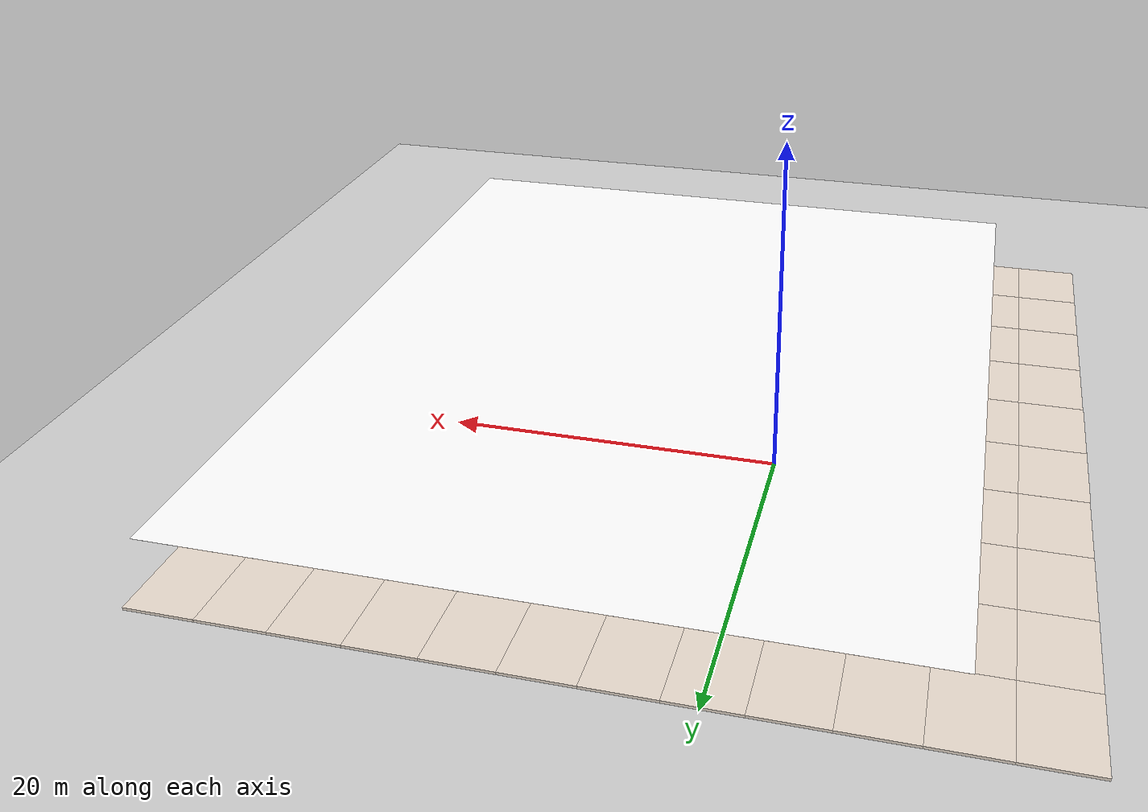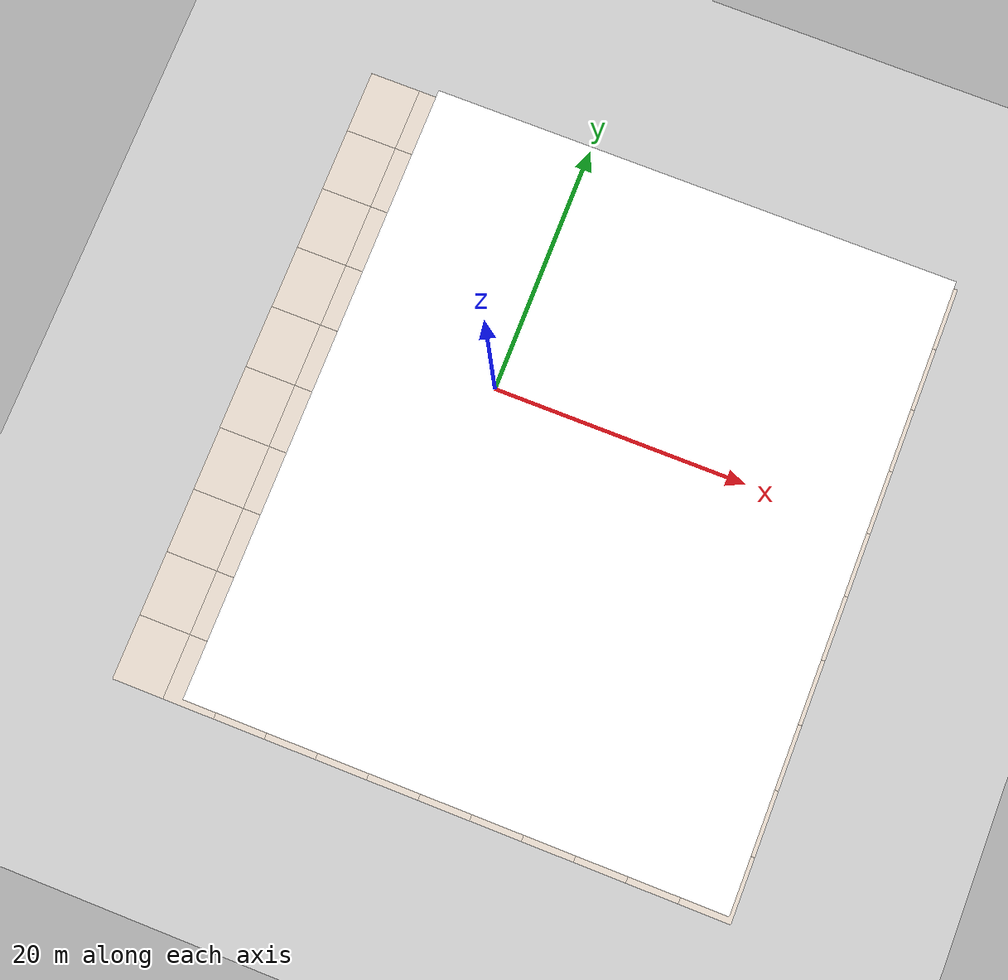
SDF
<sdf version="1.10">
 <world name="agri_world">
  <physics name="10ms" type="ignored">
   <max_step_size>0.01</max_step_size>
   <real_time_factor>1</real_time_factor>
  </physics>
  <plugin filename="gz-sim-physics-system" name="gz::sim::systems::Physics"/>
  <plugin filename="gz-sim-user-commands-system" name="gz::sim::systems::UserCommands"/>
  <plugin filename="gz-sim-scene-broadcaster-system" name="gz::sim::systems::SceneBroadcaster">
   <publish_pose>true</publish_pose>
   <publish_model_pose>true</publish_model_pose>
   <publish_link_pose>true</publish_link_pose>
  </plugin>
  <plugin filename="gz-sim-imu-system" name="gz::sim::systems::Imu"/>
  <plugin filename="gz-sim-sensors-system" name="gz::sim::systems::Sensors">
   <render_engine>ogre2</render_engine>
  </plugin>
  <scene>
   <ambient>0.800000012 0.800000012 0.800000012 1</ambient>
   <background>0.660000026 0.769999981 0.839999974 1</background>
   <grid>false</grid>
   <origin_visual>false</origin_visual>
   <shadows>true</shadows>
  </scene>
  <gravity>0 0 -9.8000000000000007</gravity>
  <magnetic_field>6.0000000000000002e-06 2.3e-05 -4.1999999999999998e-05</magnetic_field>
  <atmosphere type="adiabatic"/>
  <physics name="default_physics" default="false" type="ode">
   <max_step_size>0.001</max_step_size>
   <real_time_factor>1</real_time_factor>
   <real_time_update_rate>1000</real_time_update_rate>
  </physics>
  <scene>
   <ambient>0.400000006 0.400000006 0.400000006 1</ambient>
   <background>0.699999988 0.699999988 0.699999988 1</background>
   <shadows>true</shadows>
  </scene>
  <spherical_coordinates>
   <surface_model>EARTH_WGS84</surface_model>
   <latitude_deg>0</latitude_deg>
   <longitude_deg>0</longitude_deg>
   <elevation>0</elevation>
   <heading_deg>0</heading_deg>
  </spherical_coordinates>
  <model name="ground_plane">
   <static>true</static>
   <link name="link">
    <collision name="collision">
     <geometry><plane><normal>0 0 1</normal><size>100 100</size></plane></geometry>
     <surface><friction><ode><mu>100</mu><mu2>50</mu2></ode></friction></surface>
    </collision>
    <visual name="visual">
     <cast_shadows>false</cast_shadows>
     <geometry><plane><normal>0 0 1</normal><size>100 100</size></plane></geometry>
     <material>
      <script><uri>file://media/materials/scripts/gazebo.material</uri><name>Gazebo/Grey</name></script>
     </material>
    </visual>
    <inertial>
     <mass>1</mass>
     <inertia><ixx>1</ixx><ixy>0</ixy><ixz>0</ixz><iyy>1</iyy><iyz>0</iyz><izz>1</izz></inertia>
    </inertial>
   </link>
  </model>
  <model name="mud_box">
   <static>true</static>
   <link name="link">
    <collision name="collision"><geometry><box><size>8 10 0.20000000000000001</size></box></geometry></collision>
    <visual name="visual_1">
     <pose>-2 2.5 0 0 0 0</pose>
     <cast_shadows>false</cast_shadows>
     <geometry><box><size>4 5 0.20000000000000001</size></box></geometry>
     <material>
      <ambient>0.899999976 0.850000024 0.800000012 1</ambient>
      <diffuse>0.899999976 0.850000024 0.800000012 1</diffuse>
      <specular>0.100000001 0.100000001 0.100000001 1</specular>
      <emissive>0 0 0 1</emissive>
      <pbr><metal><albedo_map>file://mud_box/materials/textures/mud_soft_leaves.png</albedo_map></metal></pbr>
     </material>
    </visual>
    <visual name="visual_2">
     <pose>2 2.5 0 0 0 0</pose>
     <cast_shadows>false</cast_shadows>
     <geometry><box><size>4 5 0.20000000000000001</size></box></geometry>
     <material>
      <ambient>0.899999976 0.850000024 0.800000012 1</ambient>
      <diffuse>0.899999976 0.850000024 0.800000012 1</diffuse>
      <specular>0.100000001 0.100000001 0.100000001 1</specular>
      <emissive>0 0 0 1</emissive>
      <pbr><metal><albedo_map>file://mud_box/materials/textures/mud_soft_leaves.png</albedo_map></metal></pbr>
     </material>
    </visual>
    <visual name="visual_3">
     <pose>2 -2.5 0 0 0 0</pose>
     <cast_shadows>false</cast_shadows>
     <geometry><box><size>4 5 0.20000000000000001</size></box></geometry>
     <material>
      <ambient>0.899999976 0.850000024 0.800000012 1</ambient>
      <diffuse>0.899999976 0.850000024 0.800000012 1</diffuse>
      <specular>0.100000001 0.100000001 0.100000001 1</specular>
      <emissive>0 0 0 1</emissive>
      <pbr><metal><albedo_map>file://mud_box/materials/textures/mud_soft_leaves.png</albedo_map></metal></pbr>
     </material>
    </visual>
    <visual name="visual_4">
     <pose>-2 -2.5 0 0 0 0</pose>
     <cast_shadows>false</cast_shadows>
     <geometry><box><size>4 5 0.20000000000000001</size></box></geometry>
     <material>
      <ambient>0.899999976 0.850000024 0.800000012 1</ambient>
      <diffuse>0.899999976 0.850000024 0.800000012 1</diffuse>
      <specular>0.100000001 0.100000001 0.100000001 1</specular>
      <emissive>0 0 0 1</emissive>
      <pbr><metal><albedo_map>file://mud_box/materials/textures/mud_soft_leaves.png</albedo_map></metal></pbr>
     </material>
    </visual>
    <inertial>
     <mass>1</mass>
     <inertia><ixx>1</ixx><ixy>0</ixy><ixz>0</ixz><iyy>1</iyy><iyz>0</iyz><izz>1</izz></inertia>
    </inertial>
   </link>
   <pose>-6.12765 4.83622 0 0 0 0</pose>
  </model>
  <model name="mud_box_0">
   <static>true</static>
   <link name="link">
    <collision name="collision"><geometry><box><size>8 10 0.20000000000000001</size></box></geometry></collision>
    <visual name="visual_1">
     <pose>-2 2.5 0 0 0 0</pose>
     <cast_shadows>false</cast_shadows>
     <geometry><box><size>4 5 0.20000000000000001</size></box></geometry>
     <material>
      <ambient>0.899999976 0.850000024 0.800000012 1</ambient>
      <diffuse>0.899999976 0.850000024 0.800000012 1</diffuse>
      <specular>0.100000001 0.100000001 0.100000001 1</specular>
      <emissive>0 0 0 1</emissive>
      <pbr><metal><albedo_map>file://mud_box/materials/textures/mud_soft_leaves.png</albedo_map></metal></pbr>
     </material>
    </visual>
    <visual name="visual_2">
     <pose>2 2.5 0 0 0 0</pose>
     <cast_shadows>false</cast_shadows>
     <geometry><box><size>4 5 0.20000000000000001</size></box></geometry>
     <material>
      <ambient>0.899999976 0.850000024 0.800000012 1</ambient>
      <diffuse>0.899999976 0.850000024 0.800000012 1</diffuse>
      <specular>0.100000001 0.100000001 0.100000001 1</specular>
      <emissive>0 0 0 1</emissive>
      <pbr><metal><albedo_map>file://mud_box/materials/textures/mud_soft_leaves.png</albedo_map></metal></pbr>
     </material>
    </visual>
    <visual name="visual_3">
     <pose>2 -2.5 0 0 0 0</pose>
     <cast_shadows>false</cast_shadows>
     <geometry><box><size>4 5 0.20000000000000001</size></box></geometry>
     <material>
      <ambient>0.899999976 0.850000024 0.800000012 1</ambient>
      <diffuse>0.899999976 0.850000024 0.800000012 1</diffuse>
      <specular>0.100000001 0.100000001 0.100000001 1</specular>
      <emissive>0 0 0 1</emissive>
      <pbr><metal><albedo_map>file://mud_box/materials/textures/mud_soft_leaves.png</albedo_map></metal></pbr>
     </material>
    </visual>
    <visual name="visual_4">
     <pose>-2 -2.5 0 0 0 0</pose>
     <cast_shadows>false</cast_shadows>
     <geometry><box><size>4 5 0.20000000000000001</size></box></geometry>
     <material>
      <ambient>0.899999976 0.850000024 0.800000012 1</ambient>
      <diffuse>0.899999976 0.850000024 0.800000012 1</diffuse>
      <specular>0.100000001 0.100000001 0.100000001 1</specular>
      <emissive>0 0 0 1</emissive>
      <pbr><metal><albedo_map>file://mud_box/materials/textures/mud_soft_leaves.png</albedo_map></metal></pbr>
     </material>
    </visual>
    <inertial>
     <mass>1</mass>
     <inertia><ixx>1</ixx><ixy>0</ixy><ixz>0</ixz><iyy>1</iyy><iyz>0</iyz><izz>1</izz></inertia>
    </inertial>
   </link>
   <pose>1.8676699999999999 4.8310399999999998 0 0 0 0</pose>
  </model>
  <model name="mud_box_1">
   <static>true</static>
   <link name="link">
    <collision name="collision"><geometry><box><size>8 10 0.20000000000000001</size></box></geometry></collision>
    <visual name="visual_1">
     <pose>-2 2.5 0 0 0 0</pose>
     <cast_shadows>false</cast_shadows>
     <geometry><box><size>4 5 0.20000000000000001</size></box></geometry>
     <material>
      <ambient>0.899999976 0.850000024 0.800000012 1</ambient>
      <diffuse>0.899999976 0.850000024 0.800000012 1</diffuse>
      <specular>0.100000001 0.100000001 0.100000001 1</specular>
      <emissive>0 0 0 1</emissive>
      <pbr><metal><albedo_map>file://mud_box/materials/textures/mud_soft_leaves.png</albedo_map></metal></pbr>
     </material>
    </visual>
    <visual name="visual_2">
     <pose>2 2.5 0 0 0 0</pose>
     <cast_shadows>false</cast_shadows>
     <geometry><box><size>4 5 0.20000000000000001</size></box></geometry>
     <material>
      <ambient>0.899999976 0.850000024 0.800000012 1</ambient>
      <diffuse>0.899999976 0.850000024 0.800000012 1</diffuse>
      <specular>0.100000001 0.100000001 0.100000001 1</specular>
      <emissive>0 0 0 1</emissive>
      <pbr><metal><albedo_map>file://mud_box/materials/textures/mud_soft_leaves.png</albedo_map></metal></pbr>
     </material>
    </visual>
    <visual name="visual_3">
     <pose>2 -2.5 0 0 0 0</pose>
     <cast_shadows>false</cast_shadows>
     <geometry><box><size>4 5 0.20000000000000001</size></box></geometry>
     <material>
      <ambient>0.899999976 0.850000024 0.800000012 1</ambient>
      <diffuse>0.899999976 0.850000024 0.800000012 1</diffuse>
      <specular>0.100000001 0.100000001 0.100000001 1</specular>
      <emissive>0 0 0 1</emissive>
      <pbr><metal><albedo_map>file://mud_box/materials/textures/mud_soft_leaves.png</albedo_map></metal></pbr>
     </material>
    </visual>
    <visual name="visual_4">
     <pose>-2 -2.5 0 0 0 0</pose>
     <cast_shadows>false</cast_shadows>
     <geometry><box><size>4 5 0.20000000000000001</size></box></geometry>
     <material>
      <ambient>0.899999976 0.850000024 0.800000012 1</ambient>
      <diffuse>0.899999976 0.850000024 0.800000012 1</diffuse>
      <specular>0.100000001 0.100000001 0.100000001 1</specular>
      <emissive>0 0 0 1</emissive>
      <pbr><metal><albedo_map>file://mud_box/materials/textures/mud_soft_leaves.png</albedo_map></metal></pbr>
     </material>
    </visual>
    <inertial>
     <mass>1</mass>
     <inertia><ixx>1</ixx><ixy>0</ixy><ixz>0</ixz><iyy>1</iyy><iyz>0</iyz><izz>1</izz></inertia>
    </inertial>
   </link>
   <pose>-6.1279199999999996 -5.1399800000000004 0 0 0 0</pose>
  </model>
  <model name="mud_box_2">
   <static>true</static>
   <link name="link">
    <collision name="collision"><geometry><box><size>8 10 0.20000000000000001</size></box></geometry></collision>
    <visual name="visual_1">
     <pose>-2 2.5 0 0 0 0</pose>
     <cast_shadows>false</cast_shadows>
     <geometry><box><size>4 5 0.20000000000000001</size></box></geometry>
     <material>
      <ambient>0.899999976 0.850000024 0.800000012 1</ambient>
      <diffuse>0.899999976 0.850000024 0.800000012 1</diffuse>
      <specular>0.100000001 0.100000001 0.100000001 1</specular>
      <emissive>0 0 0 1</emissive>
      <pbr><metal><albedo_map>file://mud_box/materials/textures/mud_soft_leaves.png</albedo_map></metal></pbr>
     </material>
    </visual>
    <visual name="visual_2">
     <pose>2 2.5 0 0 0 0</pose>
     <cast_shadows>false</cast_shadows>
     <geometry><box><size>4 5 0.20000000000000001</size></box></geometry>
     <material>
      <ambient>0.899999976 0.850000024 0.800000012 1</ambient>
      <diffuse>0.899999976 0.850000024 0.800000012 1</diffuse>
      <specular>0.100000001 0.100000001 0.100000001 1</specular>
      <emissive>0 0 0 1</emissive>
      <pbr><metal><albedo_map>file://mud_box/materials/textures/mud_soft_leaves.png</albedo_map></metal></pbr>
     </material>
    </visual>
    <visual name="visual_3">
     <pose>2 -2.5 0 0 0 0</pose>
     <cast_shadows>false</cast_shadows>
     <geometry><box><size>4 5 0.20000000000000001</size></box></geometry>
     <material>
      <ambient>0.899999976 0.850000024 0.800000012 1</ambient>
      <diffuse>0.899999976 0.850000024 0.800000012 1</diffuse>
      <specular>0.100000001 0.100000001 0.100000001 1</specular>
      <emissive>0 0 0 1</emissive>
      <pbr><metal><albedo_map>file://mud_box/materials/textures/mud_soft_leaves.png</albedo_map></metal></pbr>
     </material>
    </visual>
    <visual name="visual_4">
     <pose>-2 -2.5 0 0 0 0</pose>
     <cast_shadows>false</cast_shadows>
     <geometry><box><size>4 5 0.20000000000000001</size></box></geometry>
     <material>
      <ambient>0.899999976 0.850000024 0.800000012 1</ambient>
      <diffuse>0.899999976 0.850000024 0.800000012 1</diffuse>
      <specular>0.100000001 0.100000001 0.100000001 1</specular>
      <emissive>0 0 0 1</emissive>
      <pbr><metal><albedo_map>file://mud_box/materials/textures/mud_soft_leaves.png</albedo_map></metal></pbr>
     </material>
    </visual>
    <inertial>
     <mass>1</mass>
     <inertia><ixx>1</ixx><ixy>0</ixy><ixz>0</ixz><iyy>1</iyy><iyz>0</iyz><izz>1</izz></inertia>
    </inertial>
   </link>
   <pose>1.85975 -5.1519199999999998 0 0 0 0</pose>
  </model>
  <model name="mud_box_3clone">
   <static>true</static>
   <link name="link">
    <collision name="collision"><geometry><box><size>8 10 0.20000000000000001</size></box></geometry></collision>
    <visual name="visual_1">
     <pose>-2 2.5 0 0 0 0</pose>
     <cast_shadows>false</cast_shadows>
     <geometry><box><size>4 5 0.20000000000000001</size></box></geometry>
     <material>
      <ambient>0.899999976 0.850000024 0.800000012 1</ambient>
      <diffuse>0.899999976 0.850000024 0.800000012 1</diffuse>
      <specular>0.100000001 0.100000001 0.100000001 1</specular>
      <emissive>0 0 0 1</emissive>
      <pbr><metal><albedo_map>file://mud_box/materials/textures/mud_soft_leaves.png</albedo_map></metal></pbr>
     </material>
    </visual>
    <visual name="visual_2">
     <pose>2 2.5 0 0 0 0</pose>
     <cast_shadows>false</cast_shadows>
     <geometry><box><size>4 5 0.20000000000000001</size></box></geometry>
     <material>
      <ambient>0.899999976 0.850000024 0.800000012 1</ambient>
      <diffuse>0.899999976 0.850000024 0.800000012 1</diffuse>
      <specular>0.100000001 0.100000001 0.100000001 1</specular>
      <emissive>0 0 0 1</emissive>
      <pbr><metal><albedo_map>file://mud_box/materials/textures/mud_soft_leaves.png</albedo_map></metal></pbr>
     </material>
    </visual>
    <visual name="visual_3">
     <pose>2 -2.5 0 0 0 0</pose>
     <cast_shadows>false</cast_shadows>
     <geometry><box><size>4 5 0.20000000000000001</size></box></geometry>
     <material>
      <ambient>0.899999976 0.850000024 0.800000012 1</ambient>
      <diffuse>0.899999976 0.850000024 0.800000012 1</diffuse>
      <specular>0.100000001 0.100000001 0.100000001 1</specular>
      <emissive>0 0 0 1</emissive>
      <pbr><metal><albedo_map>file://mud_box/materials/textures/mud_soft_leaves.png</albedo_map></metal></pbr>
     </material>
    </visual>
    <visual name="visual_4">
     <pose>-2 -2.5 0 0 0 0</pose>
     <cast_shadows>false</cast_shadows>
     <geometry><box><size>4 5 0.20000000000000001</size></box></geometry>
     <material>
      <ambient>0.899999976 0.850000024 0.800000012 1</ambient>
      <diffuse>0.899999976 0.850000024 0.800000012 1</diffuse>
      <specular>0.100000001 0.100000001 0.100000001 1</specular>
      <emissive>0 0 0 1</emissive>
      <pbr><metal><albedo_map>file://mud_box/materials/textures/mud_soft_leaves.png</albedo_map></metal></pbr>
     </material>
    </visual>
    <inertial>
     <mass>1</mass>
     <inertia><ixx>1</ixx><ixy>0</ixy><ixz>0</ixz><iyy>1</iyy><iyz>0</iyz><izz>1</izz></inertia>
    </inertial>
   </link>
   <pose>9.90 4.85 0 0 0 0</pose>
  </model>
  <model name="mud_box_0_clone">
   <static>true</static>
   <link name="link">
    <collision name="collision"><geometry><box><size>8 10 0.20000000000000001</size></box></geometry></collision>
    <visual name="visual_1">
     <pose>-2 2.5 0 0 0 0</pose>
     <cast_shadows>false</cast_shadows>
     <geometry><box><size>4 5 0.20000000000000001</size></box></geometry>
     <material>
      <ambient>0.899999976 0.850000024 0.800000012 1</ambient>
      <diffuse>0.899999976 0.850000024 0.800000012 1</diffuse>
      <specular>0.100000001 0.100000001 0.100000001 1</specular>
      <emissive>0 0 0 1</emissive>
      <pbr><metal><albedo_map>file://mud_box/materials/textures/mud_soft_leaves.png</albedo_map></metal></pbr>
     </material>
    </visual>
    <visual name="visual_2">
     <pose>2 2.5 0 0 0 0</pose>
     <cast_shadows>false</cast_shadows>
     <geometry><box><size>4 5 0.20000000000000001</size></box></geometry>
     <material>
      <ambient>0.899999976 0.850000024 0.800000012 1</ambient>
      <diffuse>0.899999976 0.850000024 0.800000012 1</diffuse>
      <specular>0.100000001 0.100000001 0.100000001 1</specular>
      <emissive>0 0 0 1</emissive>
      <pbr><metal><albedo_map>file://mud_box/materials/textures/mud_soft_leaves.png</albedo_map></metal></pbr>
     </material>
    </visual>
    <visual name="visual_3">
     <pose>2 -2.5 0 0 0 0</pose>
     <cast_shadows>false</cast_shadows>
     <geometry><box><size>4 5 0.20000000000000001</size></box></geometry>
     <material>
      <ambient>0.899999976 0.850000024 0.800000012 1</ambient>
      <diffuse>0.899999976 0.850000024 0.800000012 1</diffuse>
      <specular>0.100000001 0.100000001 0.100000001 1</specular>
      <emissive>0 0 0 1</emissive>
      <pbr><metal><albedo_map>file://mud_box/materials/textures/mud_soft_leaves.png</albedo_map></metal></pbr>
     </material>
    </visual>
    <visual name="visual_4">
     <pose>-2 -2.5 0 0 0 0</pose>
     <cast_shadows>false</cast_shadows>
     <geometry><box><size>4 5 0.20000000000000001</size></box></geometry>
     <material>
      <ambient>0.899999976 0.850000024 0.800000012 1</ambient>
      <diffuse>0.899999976 0.850000024 0.800000012 1</diffuse>
      <specular>0.100000001 0.100000001 0.100000001 1</specular>
      <emissive>0 0 0 1</emissive>
      <pbr><metal><albedo_map>file://mud_box/materials/textures/mud_soft_leaves.png</albedo_map></metal></pbr>
     </material>
    </visual>
    <inertial>
     <mass>1</mass>
     <inertia><ixx>1</ixx><ixy>0</ixy><ixz>0</ixz><iyy>1</iyy><iyz>0</iyz><izz>1</izz></inertia>
    </inertial>
   </link>
   <pose>9.8575700000000008 -5.1421599999999996 0 0 0 0</pose>
  </model>
  <model name="mud_box_0_clone_clone">
   <static>true</static>
   <link name="link">
    <collision name="collision"><geometry><box><size>8 10 0.20000000000000001</size></box></geometry></collision>
    <visual name="visual_1">
     <pose>-2 2.5 0 0 0 0</pose>
     <cast_shadows>false</cast_shadows>
     <geometry><box><size>4 5 0.20000000000000001</size></box></geometry>
     <material>
      <ambient>0.899999976 0.850000024 0.800000012 1</ambient>
      <diffuse>0.899999976 0.850000024 0.800000012 1</diffuse>
      <specular>0.100000001 0.100000001 0.100000001 1</specular>
      <emissive>0 0 0 1</emissive>
      <pbr><metal><albedo_map>file://mud_box/materials/textures/mud_soft_leaves.png</albedo_map></metal></pbr>
     </material>
    </visual>
    <visual name="visual_2">
     <pose>2 2.5 0 0 0 0</pose>
     <cast_shadows>false</cast_shadows>
     <geometry><box><size>4 5 0.20000000000000001</size></box></geometry>
     <material>
      <ambient>0.899999976 0.850000024 0.800000012 1</ambient>
      <diffuse>0.899999976 0.850000024 0.800000012 1</diffuse>
      <specular>0.100000001 0.100000001 0.100000001 1</specular>
      <emissive>0 0 0 1</emissive>
      <pbr><metal><albedo_map>file://mud_box/materials/textures/mud_soft_leaves.png</albedo_map></metal></pbr>
     </material>
    </visual>
    <visual name="visual_3">
     <pose>2 -2.5 0 0 0 0</pose>
     <cast_shadows>false</cast_shadows>
     <geometry><box><size>4 5 0.20000000000000001</size></box></geometry>
     <material>
      <ambient>0.899999976 0.850000024 0.800000012 1</ambient>
      <diffuse>0.899999976 0.850000024 0.800000012 1</diffuse>
      <specular>0.100000001 0.100000001 0.100000001 1</specular>
      <emissive>0 0 0 1</emissive>
      <pbr><metal><albedo_map>file://mud_box/materials/textures/mud_soft_leaves.png</albedo_map></metal></pbr>
     </material>
    </visual>
    <visual name="visual_4">
     <pose>-2 -2.5 0 0 0 0</pose>
     <cast_shadows>false</cast_shadows>
     <geometry><box><size>4 5 0.20000000000000001</size></box></geometry>
     <material>
      <ambient>0.899999976 0.850000024 0.800000012 1</ambient>
      <diffuse>0.899999976 0.850000024 0.800000012 1</diffuse>
      <specular>0.100000001 0.100000001 0.100000001 1</specular>
      <emissive>0 0 0 1</emissive>
      <pbr><metal><albedo_map>file://mud_box/materials/textures/mud_soft_leaves.png</albedo_map></metal></pbr>
     </material>
    </visual>
    <inertial>
     <mass>1</mass>
     <inertia><ixx>1</ixx><ixy>0</ixy><ixz>0</ixz><iyy>1</iyy><iyz>0</iyz><izz>1</izz></inertia>
    </inertial>
   </link>
   <pose>17.766100000000002 -5.1208400000000003 0 0 0 0</pose>
  </model>
  <model name="mud_box_0_clone_clone_0">
   <static>true</static>
   <link name="link">
    <collision name="collision"><geometry><box><size>8 10 0.20000000000000001</size></box></geometry></collision>
    <visual name="visual_1">
     <pose>-2 2.5 0 0 0 0</pose>
     <cast_shadows>false</cast_shadows>
     <geometry><box><size>4 5 0.20000000000000001</size></box></geometry>
     <material>
      <ambient>0.899999976 0.850000024 0.800000012 1</ambient>
      <diffuse>0.899999976 0.850000024 0.800000012 1</diffuse>
      <specular>0.100000001 0.100000001 0.100000001 1</specular>
      <emissive>0 0 0 1</emissive>
      <pbr><metal><albedo_map>file://mud_box/materials/textures/mud_soft_leaves.png</albedo_map></metal></pbr>
     </material>
    </visual>
    <visual name="visual_2">
     <pose>2 2.5 0 0 0 0</pose>
     <cast_shadows>false</cast_shadows>
     <geometry><box><size>4 5 0.20000000000000001</size></box></geometry>
     <material>
      <ambient>0.899999976 0.850000024 0.800000012 1</ambient>
      <diffuse>0.899999976 0.850000024 0.800000012 1</diffuse>
      <specular>0.100000001 0.100000001 0.100000001 1</specular>
      <emissive>0 0 0 1</emissive>
      <pbr><metal><albedo_map>file://mud_box/materials/textures/mud_soft_leaves.png</albedo_map></metal></pbr>
     </material>
    </visual>
    <visual name="visual_3">
     <pose>2 -2.5 0 0 0 0</pose>
     <cast_shadows>false</cast_shadows>
     <geometry><box><size>4 5 0.20000000000000001</size></box></geometry>
     <material>
      <ambient>0.899999976 0.850000024 0.800000012 1</ambient>
      <diffuse>0.899999976 0.850000024 0.800000012 1</diffuse>
      <specular>0.100000001 0.100000001 0.100000001 1</specular>
      <emissive>0 0 0 1</emissive>
      <pbr><metal><albedo_map>file://mud_box/materials/textures/mud_soft_leaves.png</albedo_map></metal></pbr>
     </material>
    </visual>
    <visual name="visual_4">
     <pose>-2 -2.5 0 0 0 0</pose>
     <cast_shadows>false</cast_shadows>
     <geometry><box><size>4 5 0.20000000000000001</size></box></geometry>
     <material>
      <ambient>0.899999976 0.850000024 0.800000012 1</ambient>
      <diffuse>0.899999976 0.850000024 0.800000012 1</diffuse>
      <specular>0.100000001 0.100000001 0.100000001 1</specular>
      <emissive>0 0 0 1</emissive>
      <pbr><metal><albedo_map>file://mud_box/materials/textures/mud_soft_leaves.png</albedo_map></metal></pbr>
     </material>
    </visual>
    <inertial>
     <mass>1</mass>
     <inertia><ixx>1</ixx><ixy>0</ixy><ixz>0</ixz><iyy>1</iyy><iyz>0</iyz><izz>1</izz></inertia>
    </inertial>
   </link>
   <pose>17.8432 4.7954600000000003 0 0 0 0</pose>
  </model>
  <model name="mud_box_0_clone_clone_1">
   <static>true</static>
   <link name="link">
    <collision name="collision"><geometry><box><size>8 10 0.20000000000000001</size></box></geometry></collision>
    <visual name="visual_1">
     <pose>-2 2.5 0 0 0 0</pose>
     <cast_shadows>false</cast_shadows>
     <geometry><box><size>4 5 0.20000000000000001</size></box></geometry>
     <material>
      <ambient>0.899999976 0.850000024 0.800000012 1</ambient>
      <diffuse>0.899999976 0.850000024 0.800000012 1</diffuse>
      <specular>0.100000001 0.100000001 0.100000001 1</specular>
      <emissive>0 0 0 1</emissive>
      <pbr><metal><albedo_map>file://mud_box/materials/textures/mud_soft_leaves.png</albedo_map></metal></pbr>
     </material>
    </visual>
    <visual name="visual_2">
     <pose>2 2.5 0 0 0 0</pose>
     <cast_shadows>false</cast_shadows>
     <geometry><box><size>4 5 0.20000000000000001</size></box></geometry>
     <material>
      <ambient>0.899999976 0.850000024 0.800000012 1</ambient>
      <diffuse>0.899999976 0.850000024 0.800000012 1</diffuse>
      <specular>0.100000001 0.100000001 0.100000001 1</specular>
      <emissive>0 0 0 1</emissive>
      <pbr><metal><albedo_map>file://mud_box/materials/textures/mud_soft_leaves.png</albedo_map></metal></pbr>
     </material>
    </visual>
    <visual name="visual_3">
     <pose>2 -2.5 0 0 0 0</pose>
     <cast_shadows>false</cast_shadows>
     <geometry><box><size>4 5 0.20000000000000001</size></box></geometry>
     <material>
      <ambient>0.899999976 0.850000024 0.800000012 1</ambient>
      <diffuse>0.899999976 0.850000024 0.800000012 1</diffuse>
      <specular>0.100000001 0.100000001 0.100000001 1</specular>
      <emissive>0 0 0 1</emissive>
      <pbr><metal><albedo_map>file://mud_box/materials/textures/mud_soft_leaves.png</albedo_map></metal></pbr>
     </material>
    </visual>
    <visual name="visual_4">
     <pose>-2 -2.5 0 0 0 0</pose>
     <cast_shadows>false</cast_shadows>
     <geometry><box><size>4 5 0.20000000000000001</size></box></geometry>
     <material>
      <ambient>0.899999976 0.850000024 0.800000012 1</ambient>
      <diffuse>0.899999976 0.850000024 0.800000012 1</diffuse>
      <specular>0.100000001 0.100000001 0.100000001 1</specular>
      <emissive>0 0 0 1</emissive>
      <pbr><metal><albedo_map>file://mud_box/materials/textures/mud_soft_leaves.png</albedo_map></metal></pbr>
     </material>
    </visual>
    <inertial>
     <mass>1</mass>
     <inertia><ixx>1</ixx><ixy>0</ixy><ixz>0</ixz><iyy>1</iyy><iyz>0</iyz><izz>1</izz></inertia>
    </inertial>
   </link>
   <pose>-14.127599999999999 -5.1520900000000003 0 0 0 0</pose>
  </model>
  <model name="mud_box_4">
   <static>true</static>
   <link name="link">
    <collision name="collision"><geometry><box><size>8 10 0.20000000000000001</size></box></geometry></collision>
    <visual name="visual_1">
     <pose>-2 2.5 0 0 0 0</pose>
     <cast_shadows>false</cast_shadows>
     <geometry><box><size>4 5 0.20000000000000001</size></box></geometry>
     <material>
      <ambient>0.899999976 0.850000024 0.800000012 1</ambient>
      <diffuse>0.899999976 0.850000024 0.800000012 1</diffuse>
      <specular>0.100000001 0.100000001 0.100000001 1</specular>
      <emissive>0 0 0 1</emissive>
      <pbr><metal><albedo_map>file://mud_box/materials/textures/mud_soft_leaves.png</albedo_map></metal></pbr>
     </material>
    </visual>
    <visual name="visual_2">
     <pose>2 2.5 0 0 0 0</pose>
     <cast_shadows>false</cast_shadows>
     <geometry><box><size>4 5 0.20000000000000001</size></box></geometry>
     <material>
      <ambient>0.899999976 0.850000024 0.800000012 1</ambient>
      <diffuse>0.899999976 0.850000024 0.800000012 1</diffuse>
      <specular>0.100000001 0.100000001 0.100000001 1</specular>
      <emissive>0 0 0 1</emissive>
      <pbr><metal><albedo_map>file://mud_box/materials/textures/mud_soft_leaves.png</albedo_map></metal></pbr>
     </material>
    </visual>
    <visual name="visual_3">
     <pose>2 -2.5 0 0 0 0</pose>
     <cast_shadows>false</cast_shadows>
     <geometry><box><size>4 5 0.20000000000000001</size></box></geometry>
     <material>
      <ambient>0.899999976 0.850000024 0.800000012 1</ambient>
      <diffuse>0.899999976 0.850000024 0.800000012 1</diffuse>
      <specular>0.100000001 0.100000001 0.100000001 1</specular>
      <emissive>0 0 0 1</emissive>
      <pbr><metal><albedo_map>file://mud_box/materials/textures/mud_soft_leaves.png</albedo_map></metal></pbr>
     </material>
    </visual>
    <visual name="visual_4">
     <pose>-2 -2.5 0 0 0 0</pose>
     <cast_shadows>false</cast_shadows>
     <geometry><box><size>4 5 0.20000000000000001</size></box></geometry>
     <material>
      <ambient>0.899999976 0.850000024 0.800000012 1</ambient>
      <diffuse>0.899999976 0.850000024 0.800000012 1</diffuse>
      <specular>0.100000001 0.100000001 0.100000001 1</specular>
      <emissive>0 0 0 1</emissive>
      <pbr><metal><albedo_map>file://mud_box/materials/textures/mud_soft_leaves.png</albedo_map></metal></pbr>
     </material>
    </visual>
    <inertial>
     <mass>1</mass>
     <inertia><ixx>1</ixx><ixy>0</ixy><ixz>0</ixz><iyy>1</iyy><iyz>0</iyz><izz>1</izz></inertia>
    </inertial>
   </link>
   <pose>-14.1 14.85 0 0 0 0</pose>
  </model>
  <model name="mud_box_5">
   <static>true</static>
   <link name="link">
    <collision name="collision"><geometry><box><size>8 10 0.20000000000000001</size></box></geometry></collision>
    <visual name="visual_1">
     <pose>-2 2.5 0 0 0 0</pose>
     <cast_shadows>false</cast_shadows>
     <geometry><box><size>4 5 0.20000000000000001</size></box></geometry>
     <material>
      <ambient>0.899999976 0.850000024 0.800000012 1</ambient>
      <diffuse>0.899999976 0.850000024 0.800000012 1</diffuse>
      <specular>0.100000001 0.100000001 0.100000001 1</specular>
      <emissive>0 0 0 1</emissive>
      <pbr><metal><albedo_map>file://mud_box/materials/textures/mud_soft_leaves.png</albedo_map></metal></pbr>
     </material>
    </visual>
    <visual name="visual_2">
     <pose>2 2.5 0 0 0 0</pose>
     <cast_shadows>false</cast_shadows>
     <geometry><box><size>4 5 0.20000000000000001</size></box></geometry>
     <material>
      <ambient>0.899999976 0.850000024 0.800000012 1</ambient>
      <diffuse>0.899999976 0.850000024 0.800000012 1</diffuse>
      <specular>0.100000001 0.100000001 0.100000001 1</specular>
      <emissive>0 0 0 1</emissive>
      <pbr><metal><albedo_map>file://mud_box/materials/textures/mud_soft_leaves.png</albedo_map></metal></pbr>
     </material>
    </visual>
    <visual name="visual_3">
     <pose>2 -2.5 0 0 0 0</pose>
     <cast_shadows>false</cast_shadows>
     <geometry><box><size>4 5 0.20000000000000001</size></box></geometry>
     <material>
      <ambient>0.899999976 0.850000024 0.800000012 1</ambient>
      <diffuse>0.899999976 0.850000024 0.800000012 1</diffuse>
      <specular>0.100000001 0.100000001 0.100000001 1</specular>
      <emissive>0 0 0 1</emissive>
      <pbr><metal><albedo_map>file://mud_box/materials/textures/mud_soft_leaves.png</albedo_map></metal></pbr>
     </material>
    </visual>
    <visual name="visual_4">
     <pose>-2 -2.5 0 0 0 0</pose>
     <cast_shadows>false</cast_shadows>
     <geometry><box><size>4 5 0.20000000000000001</size></box></geometry>
     <material>
      <ambient>0.899999976 0.850000024 0.800000012 1</ambient>
      <diffuse>0.899999976 0.850000024 0.800000012 1</diffuse>
      <specular>0.100000001 0.100000001 0.100000001 1</specular>
      <emissive>0 0 0 1</emissive>
      <pbr><metal><albedo_map>file://mud_box/materials/textures/mud_soft_leaves.png</albedo_map></metal></pbr>
     </material>
    </visual>
    <inertial>
     <mass>1</mass>
     <inertia><ixx>1</ixx><ixy>0</ixy><ixz>0</ixz><iyy>1</iyy><iyz>0</iyz><izz>1</izz></inertia>
    </inertial>
   </link>
   <pose>-6.0999999999999996 14.85 0 0 0 0</pose>
  </model>
  <model name="mud_box_6">
   <static>true</static>
   <link name="link">
    <collision name="collision"><geometry><box><size>8 10 0.20000000000000001</size></box></geometry></collision>
    <visual name="visual_1">
     <pose>-2 2.5 0 0 0 0</pose>
     <cast_shadows>false</cast_shadows>
     <geometry><box><size>4 5 0.20000000000000001</size></box></geometry>
     <material>
      <ambient>0.899999976 0.850000024 0.800000012 1</ambient>
      <diffuse>0.899999976 0.850000024 0.800000012 1</diffuse>
      <specular>0.100000001 0.100000001 0.100000001 1</specular>
      <emissive>0 0 0 1</emissive>
      <pbr><metal><albedo_map>file://mud_box/materials/textures/mud_soft_leaves.png</albedo_map></metal></pbr>
     </material>
    </visual>
    <visual name="visual_2">
     <pose>2 2.5 0 0 0 0</pose>
     <cast_shadows>false</cast_shadows>
     <geometry><box><size>4 5 0.20000000000000001</size></box></geometry>
     <material>
      <ambient>0.899999976 0.850000024 0.800000012 1</ambient>
      <diffuse>0.899999976 0.850000024 0.800000012 1</diffuse>
      <specular>0.100000001 0.100000001 0.100000001 1</specular>
      <emissive>0 0 0 1</emissive>
      <pbr><metal><albedo_map>file://mud_box/materials/textures/mud_soft_leaves.png</albedo_map></metal></pbr>
     </material>
    </visual>
    <visual name="visual_3">
     <pose>2 -2.5 0 0 0 0</pose>
     <cast_shadows>false</cast_shadows>
     <geometry><box><size>4 5 0.20000000000000001</size></box></geometry>
     <material>
      <ambient>0.899999976 0.850000024 0.800000012 1</ambient>
      <diffuse>0.899999976 0.850000024 0.800000012 1</diffuse>
      <specular>0.100000001 0.100000001 0.100000001 1</specular>
      <emissive>0 0 0 1</emissive>
      <pbr><metal><albedo_map>file://mud_box/materials/textures/mud_soft_leaves.png</albedo_map></metal></pbr>
     </material>
    </visual>
    <visual name="visual_4">
     <pose>-2 -2.5 0 0 0 0</pose>
     <cast_shadows>false</cast_shadows>
     <geometry><box><size>4 5 0.20000000000000001</size></box></geometry>
     <material>
      <ambient>0.899999976 0.850000024 0.800000012 1</ambient>
      <diffuse>0.899999976 0.850000024 0.800000012 1</diffuse>
      <specular>0.100000001 0.100000001 0.100000001 1</specular>
      <emissive>0 0 0 1</emissive>
      <pbr><metal><albedo_map>file://mud_box/materials/textures/mud_soft_leaves.png</albedo_map></metal></pbr>
     </material>
    </visual>
    <inertial>
     <mass>1</mass>
     <inertia><ixx>1</ixx><ixy>0</ixy><ixz>0</ixz><iyy>1</iyy><iyz>0</iyz><izz>1</izz></inertia>
    </inertial>
   </link>
   <pose>9.9000000000000004 14.85 0 0 0 0</pose>
  </model>
  <model name="mud_box_7">
   <static>true</static>
   <link name="link">
    <collision name="collision"><geometry><box><size>8 10 0.20000000000000001</size></box></geometry></collision>
    <visual name="visual_1">
     <pose>-2 2.5 0 0 0 0</pose>
     <cast_shadows>false</cast_shadows>
     <geometry><box><size>4 5 0.20000000000000001</size></box></geometry>
     <material>
      <ambient>0.899999976 0.850000024 0.800000012 1</ambient>
      <diffuse>0.899999976 0.850000024 0.800000012 1</diffuse>
      <specular>0.100000001 0.100000001 0.100000001 1</specular>
      <emissive>0 0 0 1</emissive>
      <pbr><metal><albedo_map>file://mud_box/materials/textures/mud_soft_leaves.png</albedo_map></metal></pbr>
     </material>
    </visual>
    <visual name="visual_2">
     <pose>2 2.5 0 0 0 0</pose>
     <cast_shadows>false</cast_shadows>
     <geometry><box><size>4 5 0.20000000000000001</size></box></geometry>
     <material>
      <ambient>0.899999976 0.850000024 0.800000012 1</ambient>
      <diffuse>0.899999976 0.850000024 0.800000012 1</diffuse>
      <specular>0.100000001 0.100000001 0.100000001 1</specular>
      <emissive>0 0 0 1</emissive>
      <pbr><metal><albedo_map>file://mud_box/materials/textures/mud_soft_leaves.png</albedo_map></metal></pbr>
     </material>
    </visual>
    <visual name="visual_3">
     <pose>2 -2.5 0 0 0 0</pose>
     <cast_shadows>false</cast_shadows>
     <geometry><box><size>4 5 0.20000000000000001</size></box></geometry>
     <material>
      <ambient>0.899999976 0.850000024 0.800000012 1</ambient>
      <diffuse>0.899999976 0.850000024 0.800000012 1</diffuse>
      <specular>0.100000001 0.100000001 0.100000001 1</specular>
      <emissive>0 0 0 1</emissive>
      <pbr><metal><albedo_map>file://mud_box/materials/textures/mud_soft_leaves.png</albedo_map></metal></pbr>
     </material>
    </visual>
    <visual name="visual_4">
     <pose>-2 -2.5 0 0 0 0</pose>
     <cast_shadows>false</cast_shadows>
     <geometry><box><size>4 5 0.20000000000000001</size></box></geometry>
     <material>
      <ambient>0.899999976 0.850000024 0.800000012 1</ambient>
      <diffuse>0.899999976 0.850000024 0.800000012 1</diffuse>
      <specular>0.100000001 0.100000001 0.100000001 1</specular>
      <emissive>0 0 0 1</emissive>
      <pbr><metal><albedo_map>file://mud_box/materials/textures/mud_soft_leaves.png</albedo_map></metal></pbr>
     </material>
    </visual>
    <inertial>
     <mass>1</mass>
     <inertia><ixx>1</ixx><ixy>0</ixy><ixz>0</ixz><iyy>1</iyy><iyz>0</iyz><izz>1</izz></inertia>
    </inertial>
   </link>
   <pose>17.899999999999999 14.85 0 0 0 0</pose>
  </model>
  <model name="mud_box_8">
   <static>true</static>
   <link name="link">
    <collision name="collision"><geometry><box><size>8 10 0.20000000000000001</size></box></geometry></collision>
    <visual name="visual_1">
     <pose>-2 2.5 0 0 0 0</pose>
     <cast_shadows>false</cast_shadows>
     <geometry><box><size>4 5 0.20000000000000001</size></box></geometry>
     <material>
      <ambient>0.899999976 0.850000024 0.800000012 1</ambient>
      <diffuse>0.899999976 0.850000024 0.800000012 1</diffuse>
      <specular>0.100000001 0.100000001 0.100000001 1</specular>
      <emissive>0 0 0 1</emissive>
      <pbr><metal><albedo_map>file://mud_box/materials/textures/mud_soft_leaves.png</albedo_map></metal></pbr>
     </material>
    </visual>
    <visual name="visual_2">
     <pose>2 2.5 0 0 0 0</pose>
     <cast_shadows>false</cast_shadows>
     <geometry><box><size>4 5 0.20000000000000001</size></box></geometry>
     <material>
      <ambient>0.899999976 0.850000024 0.800000012 1</ambient>
      <diffuse>0.899999976 0.850000024 0.800000012 1</diffuse>
      <specular>0.100000001 0.100000001 0.100000001 1</specular>
      <emissive>0 0 0 1</emissive>
      <pbr><metal><albedo_map>file://mud_box/materials/textures/mud_soft_leaves.png</albedo_map></metal></pbr>
     </material>
    </visual>
    <visual name="visual_3">
     <pose>2 -2.5 0 0 0 0</pose>
     <cast_shadows>false</cast_shadows>
     <geometry><box><size>4 5 0.20000000000000001</size></box></geometry>
     <material>
      <ambient>0.899999976 0.850000024 0.800000012 1</ambient>
      <diffuse>0.899999976 0.850000024 0.800000012 1</diffuse>
      <specular>0.100000001 0.100000001 0.100000001 1</specular>
      <emissive>0 0 0 1</emissive>
      <pbr><metal><albedo_map>file://mud_box/materials/textures/mud_soft_leaves.png</albedo_map></metal></pbr>
     </material>
    </visual>
    <visual name="visual_4">
     <pose>-2 -2.5 0 0 0 0</pose>
     <cast_shadows>false</cast_shadows>
     <geometry><box><size>4 5 0.20000000000000001</size></box></geometry>
     <material>
      <ambient>0.899999976 0.850000024 0.800000012 1</ambient>
      <diffuse>0.899999976 0.850000024 0.800000012 1</diffuse>
      <specular>0.100000001 0.100000001 0.100000001 1</specular>
      <emissive>0 0 0 1</emissive>
      <pbr><metal><albedo_map>file://mud_box/materials/textures/mud_soft_leaves.png</albedo_map></metal></pbr>
     </material>
    </visual>
    <inertial>
     <mass>1</mass>
     <inertia><ixx>1</ixx><ixy>0</ixy><ixz>0</ixz><iyy>1</iyy><iyz>0</iyz><izz>1</izz></inertia>
    </inertial>
   </link>
   <pose>1.8999999999999999 14.85 0 0 0 0</pose>
  </model>
  <model name="mud_box_0_clone_clone_1_1">
   <static>true</static>
   <link name="link">
    <collision name="collision"><geometry><box><size>8 10 0.20000000000000001</size></box></geometry></collision>
    <visual name="visual_1">
     <pose>-2 2.5 0 0 0 0</pose>
     <cast_shadows>false</cast_shadows>
     <geometry><box><size>4 5 0.20000000000000001</size></box></geometry>
     <material>
      <ambient>0.899999976 0.850000024 0.800000012 1</ambient>
      <diffuse>0.899999976 0.850000024 0.800000012 1</diffuse>
      <specular>0.100000001 0.100000001 0.100000001 1</specular>
      <emissive>0 0 0 1</emissive>
      <pbr><metal><albedo_map>file://mud_box/materials/textures/mud_soft_leaves.png</albedo_map></metal></pbr>
     </material>
    </visual>
    <visual name="visual_2">
     <pose>2 2.5 0 0 0 0</pose>
     <cast_shadows>false</cast_shadows>
     <geometry><box><size>4 5 0.20000000000000001</size></box></geometry>
     <material>
      <ambient>0.899999976 0.850000024 0.800000012 1</ambient>
      <diffuse>0.899999976 0.850000024 0.800000012 1</diffuse>
      <specular>0.100000001 0.100000001 0.100000001 1</specular>
      <emissive>0 0 0 1</emissive>
      <pbr><metal><albedo_map>file://mud_box/materials/textures/mud_soft_leaves.png</albedo_map></metal></pbr>
     </material>
    </visual>
    <visual name="visual_3">
     <pose>2 -2.5 0 0 0 0</pose>
     <cast_shadows>false</cast_shadows>
     <geometry><box><size>4 5 0.20000000000000001</size></box></geometry>
     <material>
      <ambient>0.899999976 0.850000024 0.800000012 1</ambient>
      <diffuse>0.899999976 0.850000024 0.800000012 1</diffuse>
      <specular>0.100000001 0.100000001 0.100000001 1</specular>
      <emissive>0 0 0 1</emissive>
      <pbr><metal><albedo_map>file://mud_box/materials/textures/mud_soft_leaves.png</albedo_map></metal></pbr>
     </material>
    </visual>
    <visual name="visual_4">
     <pose>-2 -2.5 0 0 0 0</pose>
     <cast_shadows>false</cast_shadows>
     <geometry><box><size>4 5 0.20000000000000001</size></box></geometry>
     <material>
      <ambient>0.899999976 0.850000024 0.800000012 1</ambient>
      <diffuse>0.899999976 0.850000024 0.800000012 1</diffuse>
      <specular>0.100000001 0.100000001 0.100000001 1</specular>
      <emissive>0 0 0 1</emissive>
      <pbr><metal><albedo_map>file://mud_box/materials/textures/mud_soft_leaves.png</albedo_map></metal></pbr>
     </material>
    </visual>
    <inertial>
     <mass>1</mass>
     <inertia><ixx>1</ixx><ixy>0</ixy><ixz>0</ixz><iyy>1</iyy><iyz>0</iyz><izz>1</izz></inertia>
    </inertial>
   </link>
   <pose>-14.1 -15.15 0 0 0 0</pose>
  </model>
  <model name="mud_box_0_clone_clone_1_2">
   <static>true</static>
   <link name="link">
    <collision name="collision"><geometry><box><size>8 10 0.20000000000000001</size></box></geometry></collision>
    <visual name="visual_1">
     <pose>-2 2.5 0 0 0 0</pose>
     <cast_shadows>false</cast_shadows>
     <geometry><box><size>4 5 0.20000000000000001</size></box></geometry>
     <material>
      <ambient>0.899999976 0.850000024 0.800000012 1</ambient>
      <diffuse>0.899999976 0.850000024 0.800000012 1</diffuse>
      <specular>0.100000001 0.100000001 0.100000001 1</specular>
      <emissive>0 0 0 1</emissive>
      <pbr><metal><albedo_map>file://mud_box/materials/textures/mud_soft_leaves.png</albedo_map></metal></pbr>
     </material>
    </visual>
    <visual name="visual_2">
     <pose>2 2.5 0 0 0 0</pose>
     <cast_shadows>false</cast_shadows>
     <geometry><box><size>4 5 0.20000000000000001</size></box></geometry>
     <material>
      <ambient>0.899999976 0.850000024 0.800000012 1</ambient>
      <diffuse>0.899999976 0.850000024 0.800000012 1</diffuse>
      <specular>0.100000001 0.100000001 0.100000001 1</specular>
      <emissive>0 0 0 1</emissive>
      <pbr><metal><albedo_map>file://mud_box/materials/textures/mud_soft_leaves.png</albedo_map></metal></pbr>
     </material>
    </visual>
    <visual name="visual_3">
     <pose>2 -2.5 0 0 0 0</pose>
     <cast_shadows>false</cast_shadows>
     <geometry><box><size>4 5 0.20000000000000001</size></box></geometry>
     <material>
      <ambient>0.899999976 0.850000024 0.800000012 1</ambient>
      <diffuse>0.899999976 0.850000024 0.800000012 1</diffuse>
      <specular>0.100000001 0.100000001 0.100000001 1</specular>
      <emissive>0 0 0 1</emissive>
      <pbr><metal><albedo_map>file://mud_box/materials/textures/mud_soft_leaves.png</albedo_map></metal></pbr>
     </material>
    </visual>
    <visual name="visual_4">
     <pose>-2 -2.5 0 0 0 0</pose>
     <cast_shadows>false</cast_shadows>
     <geometry><box><size>4 5 0.20000000000000001</size></box></geometry>
     <material>
      <ambient>0.899999976 0.850000024 0.800000012 1</ambient>
      <diffuse>0.899999976 0.850000024 0.800000012 1</diffuse>
      <specular>0.100000001 0.100000001 0.100000001 1</specular>
      <emissive>0 0 0 1</emissive>
      <pbr><metal><albedo_map>file://mud_box/materials/textures/mud_soft_leaves.png</albedo_map></metal></pbr>
     </material>
    </visual>
    <inertial>
     <mass>1</mass>
     <inertia><ixx>1</ixx><ixy>0</ixy><ixz>0</ixz><iyy>1</iyy><iyz>0</iyz><izz>1</izz></inertia>
    </inertial>
   </link>
   <pose>-6.0999999999999996 -15.15 0 0 0 0</pose>
  </model>
  <model name="mud_box_0_clone_clone_1_3">
   <static>true</static>
   <link name="link">
    <collision name="collision"><geometry><box><size>8 10 0.20000000000000001</size></box></geometry></collision>
    <visual name="visual_1">
     <pose>-2 2.5 0 0 0 0</pose>
     <cast_shadows>false</cast_shadows>
     <geometry><box><size>4 5 0.20000000000000001</size></box></geometry>
     <material>
      <ambient>0.899999976 0.850000024 0.800000012 1</ambient>
      <diffuse>0.899999976 0.850000024 0.800000012 1</diffuse>
      <specular>0.100000001 0.100000001 0.100000001 1</specular>
      <emissive>0 0 0 1</emissive>
      <pbr><metal><albedo_map>file://mud_box/materials/textures/mud_soft_leaves.png</albedo_map></metal></pbr>
     </material>
    </visual>
    <visual name="visual_2">
     <pose>2 2.5 0 0 0 0</pose>
     <cast_shadows>false</cast_shadows>
     <geometry><box><size>4 5 0.20000000000000001</size></box></geometry>
     <material>
      <ambient>0.899999976 0.850000024 0.800000012 1</ambient>
      <diffuse>0.899999976 0.850000024 0.800000012 1</diffuse>
      <specular>0.100000001 0.100000001 0.100000001 1</specular>
      <emissive>0 0 0 1</emissive>
      <pbr><metal><albedo_map>file://mud_box/materials/textures/mud_soft_leaves.png</albedo_map></metal></pbr>
     </material>
    </visual>
    <visual name="visual_3">
     <pose>2 -2.5 0 0 0 0</pose>
     <cast_shadows>false</cast_shadows>
     <geometry><box><size>4 5 0.20000000000000001</size></box></geometry>
     <material>
      <ambient>0.899999976 0.850000024 0.800000012 1</ambient>
      <diffuse>0.899999976 0.850000024 0.800000012 1</diffuse>
      <specular>0.100000001 0.100000001 0.100000001 1</specular>
      <emissive>0 0 0 1</emissive>
      <pbr><metal><albedo_map>file://mud_box/materials/textures/mud_soft_leaves.png</albedo_map></metal></pbr>
     </material>
    </visual>
    <visual name="visual_4">
     <pose>-2 -2.5 0 0 0 0</pose>
     <cast_shadows>false</cast_shadows>
     <geometry><box><size>4 5 0.20000000000000001</size></box></geometry>
     <material>
      <ambient>0.899999976 0.850000024 0.800000012 1</ambient>
      <diffuse>0.899999976 0.850000024 0.800000012 1</diffuse>
      <specular>0.100000001 0.100000001 0.100000001 1</specular>
      <emissive>0 0 0 1</emissive>
      <pbr><metal><albedo_map>file://mud_box/materials/textures/mud_soft_leaves.png</albedo_map></metal></pbr>
     </material>
    </visual>
    <inertial>
     <mass>1</mass>
     <inertia><ixx>1</ixx><ixy>0</ixy><ixz>0</ixz><iyy>1</iyy><iyz>0</iyz><izz>1</izz></inertia>
    </inertial>
   </link>
   <pose>1.8999999999999999 -15.15 0 0 0 0</pose>
  </model>
  <model name="mud_box_0_clone_clone_1_4">
   <static>true</static>
   <link name="link">
    <collision name="collision"><geometry><box><size>8 10 0.20000000000000001</size></box></geometry></collision>
    <visual name="visual_1">
     <pose>-2 2.5 0 0 0 0</pose>
     <cast_shadows>false</cast_shadows>
     <geometry><box><size>4 5 0.20000000000000001</size></box></geometry>
     <material>
      <ambient>0.899999976 0.850000024 0.800000012 1</ambient>
      <diffuse>0.899999976 0.850000024 0.800000012 1</diffuse>
      <specular>0.100000001 0.100000001 0.100000001 1</specular>
      <emissive>0 0 0 1</emissive>
      <pbr><metal><albedo_map>file://mud_box/materials/textures/mud_soft_leaves.png</albedo_map></metal></pbr>
     </material>
    </visual>
    <visual name="visual_2">
     <pose>2 2.5 0 0 0 0</pose>
     <cast_shadows>false</cast_shadows>
     <geometry><box><size>4 5 0.20000000000000001</size></box></geometry>
     <material>
      <ambient>0.899999976 0.850000024 0.800000012 1</ambient>
      <diffuse>0.899999976 0.850000024 0.800000012 1</diffuse>
      <specular>0.100000001 0.100000001 0.100000001 1</specular>
      <emissive>0 0 0 1</emissive>
      <pbr><metal><albedo_map>file://mud_box/materials/textures/mud_soft_leaves.png</albedo_map></metal></pbr>
     </material>
    </visual>
    <visual name="visual_3">
     <pose>2 -2.5 0 0 0 0</pose>
     <cast_shadows>false</cast_shadows>
     <geometry><box><size>4 5 0.20000000000000001</size></box></geometry>
     <material>
      <ambient>0.899999976 0.850000024 0.800000012 1</ambient>
      <diffuse>0.899999976 0.850000024 0.800000012 1</diffuse>
      <specular>0.100000001 0.100000001 0.100000001 1</specular>
      <emissive>0 0 0 1</emissive>
      <pbr><metal><albedo_map>file://mud_box/materials/textures/mud_soft_leaves.png</albedo_map></metal></pbr>
     </material>
    </visual>
    <visual name="visual_4">
     <pose>-2 -2.5 0 0 0 0</pose>
     <cast_shadows>false</cast_shadows>
     <geometry><box><size>4 5 0.20000000000000001</size></box></geometry>
     <material>
      <ambient>0.899999976 0.850000024 0.800000012 1</ambient>
      <diffuse>0.899999976 0.850000024 0.800000012 1</diffuse>
      <specular>0.100000001 0.100000001 0.100000001 1</specular>
      <emissive>0 0 0 1</emissive>
      <pbr><metal><albedo_map>file://mud_box/materials/textures/mud_soft_leaves.png</albedo_map></metal></pbr>
     </material>
    </visual>
    <inertial>
     <mass>1</mass>
     <inertia><ixx>1</ixx><ixy>0</ixy><ixz>0</ixz><iyy>1</iyy><iyz>0</iyz><izz>1</izz></inertia>
    </inertial>
   </link>
   <pose>9.9000000000000004 -15.15 0 0 0 0</pose>
  </model>
  <model name="mud_box_0_clone_clone_1_5">
   <static>true</static>
   <link name="link">
    <collision name="collision"><geometry><box><size>8 10 0.20000000000000001</size></box></geometry></collision>
    <visual name="visual_1">
     <pose>-2 2.5 0 0 0 0</pose>
     <cast_shadows>false</cast_shadows>
     <geometry><box><size>4 5 0.20000000000000001</size></box></geometry>
     <material>
      <ambient>0.899999976 0.850000024 0.800000012 1</ambient>
      <diffuse>0.899999976 0.850000024 0.800000012 1</diffuse>
      <specular>0.100000001 0.100000001 0.100000001 1</specular>
      <emissive>0 0 0 1</emissive>
      <pbr><metal><albedo_map>file://mud_box/materials/textures/mud_soft_leaves.png</albedo_map></metal></pbr>
     </material>
    </visual>
    <visual name="visual_2">
     <pose>2 2.5 0 0 0 0</pose>
     <cast_shadows>false</cast_shadows>
     <geometry><box><size>4 5 0.20000000000000001</size></box></geometry>
     <material>
      <ambient>0.899999976 0.850000024 0.800000012 1</ambient>
      <diffuse>0.899999976 0.850000024 0.800000012 1</diffuse>
      <specular>0.100000001 0.100000001 0.100000001 1</specular>
      <emissive>0 0 0 1</emissive>
      <pbr><metal><albedo_map>file://mud_box/materials/textures/mud_soft_leaves.png</albedo_map></metal></pbr>
     </material>
    </visual>
    <visual name="visual_3">
     <pose>2 -2.5 0 0 0 0</pose>
     <cast_shadows>false</cast_shadows>
     <geometry><box><size>4 5 0.20000000000000001</size></box></geometry>
     <material>
      <ambient>0.899999976 0.850000024 0.800000012 1</ambient>
      <diffuse>0.899999976 0.850000024 0.800000012 1</diffuse>
      <specular>0.100000001 0.100000001 0.100000001 1</specular>
      <emissive>0 0 0 1</emissive>
      <pbr><metal><albedo_map>file://mud_box/materials/textures/mud_soft_leaves.png</albedo_map></metal></pbr>
     </material>
    </visual>
    <visual name="visual_4">
     <pose>-2 -2.5 0 0 0 0</pose>
     <cast_shadows>false</cast_shadows>
     <geometry><box><size>4 5 0.20000000000000001</size></box></geometry>
     <material>
      <ambient>0.899999976 0.850000024 0.800000012 1</ambient>
      <diffuse>0.899999976 0.850000024 0.800000012 1</diffuse>
      <specular>0.100000001 0.100000001 0.100000001 1</specular>
      <emissive>0 0 0 1</emissive>
      <pbr><metal><albedo_map>file://mud_box/materials/textures/mud_soft_leaves.png</albedo_map></metal></pbr>
     </material>
    </visual>
    <inertial>
     <mass>1</mass>
     <inertia><ixx>1</ixx><ixy>0</ixy><ixz>0</ixz><iyy>1</iyy><iyz>0</iyz><izz>1</izz></inertia>
    </inertial>
   </link>
   <pose>17.899999999999999 -15.15 0 0 0 0</pose>
  </model>
  <model name="mud_box_0_clone_clone_1_6">
   <static>true</static>
   <link name="link">
    <collision name="collision"><geometry><box><size>8 10 0.20000000000000001</size></box></geometry></collision>
    <visual name="visual_1">
     <pose>-2 2.5 0 0 0 0</pose>
     <cast_shadows>false</cast_shadows>
     <geometry><box><size>4 5 0.20000000000000001</size></box></geometry>
     <material>
      <ambient>0.899999976 0.850000024 0.800000012 1</ambient>
      <diffuse>0.899999976 0.850000024 0.800000012 1</diffuse>
      <specular>0.100000001 0.100000001 0.100000001 1</specular>
      <emissive>0 0 0 1</emissive>
      <pbr><metal><albedo_map>file://mud_box/materials/textures/mud_soft_leaves.png</albedo_map></metal></pbr>
     </material>
    </visual>
    <visual name="visual_2">
     <pose>2 2.5 0 0 0 0</pose>
     <cast_shadows>false</cast_shadows>
     <geometry><box><size>4 5 0.20000000000000001</size></box></geometry>
     <material>
      <ambient>0.899999976 0.850000024 0.800000012 1</ambient>
      <diffuse>0.899999976 0.850000024 0.800000012 1</diffuse>
      <specular>0.100000001 0.100000001 0.100000001 1</specular>
      <emissive>0 0 0 1</emissive>
      <pbr><metal><albedo_map>file://mud_box/materials/textures/mud_soft_leaves.png</albedo_map></metal></pbr>
     </material>
    </visual>
    <visual name="visual_3">
     <pose>2 -2.5 0 0 0 0</pose>
     <cast_shadows>false</cast_shadows>
     <geometry><box><size>4 5 0.20000000000000001</size></box></geometry>
     <material>
      <ambient>0.899999976 0.850000024 0.800000012 1</ambient>
      <diffuse>0.899999976 0.850000024 0.800000012 1</diffuse>
      <specular>0.100000001 0.100000001 0.100000001 1</specular>
      <emissive>0 0 0 1</emissive>
      <pbr><metal><albedo_map>file://mud_box/materials/textures/mud_soft_leaves.png</albedo_map></metal></pbr>
     </material>
    </visual>
    <visual name="visual_4">
     <pose>-2 -2.5 0 0 0 0</pose>
     <cast_shadows>false</cast_shadows>
     <geometry><box><size>4 5 0.20000000000000001</size></box></geometry>
     <material>
      <ambient>0.899999976 0.850000024 0.800000012 1</ambient>
      <diffuse>0.899999976 0.850000024 0.800000012 1</diffuse>
      <specular>0.100000001 0.100000001 0.100000001 1</specular>
      <emissive>0 0 0 1</emissive>
      <pbr><metal><albedo_map>file://mud_box/materials/textures/mud_soft_leaves.png</albedo_map></metal></pbr>
     </material>
    </visual>
    <inertial>
     <mass>1</mass>
     <inertia><ixx>1</ixx><ixy>0</ixy><ixz>0</ixz><iyy>1</iyy><iyz>0</iyz><izz>1</izz></inertia>
    </inertial>
   </link>
   <pose>-14.1 -25.149999999999999 0 0 0 0</pose>
  </model>
  <model name="mud_box_0_clone_clone_1_7">
   <static>true</static>
   <link name="link">
    <collision name="collision"><geometry><box><size>8 10 0.20000000000000001</size></box></geometry></collision>
    <visual name="visual_1">
     <pose>-2 2.5 0 0 0 0</pose>
     <cast_shadows>false</cast_shadows>
     <geometry><box><size>4 5 0.20000000000000001</size></box></geometry>
     <material>
      <ambient>0.899999976 0.850000024 0.800000012 1</ambient>
      <diffuse>0.899999976 0.850000024 0.800000012 1</diffuse>
      <specular>0.100000001 0.100000001 0.100000001 1</specular>
      <emissive>0 0 0 1</emissive>
      <pbr><metal><albedo_map>file://mud_box/materials/textures/mud_soft_leaves.png</albedo_map></metal></pbr>
     </material>
    </visual>
    <visual name="visual_2">
     <pose>2 2.5 0 0 0 0</pose>
     <cast_shadows>false</cast_shadows>
     <geometry><box><size>4 5 0.20000000000000001</size></box></geometry>
     <material>
      <ambient>0.899999976 0.850000024 0.800000012 1</ambient>
      <diffuse>0.899999976 0.850000024 0.800000012 1</diffuse>
      <specular>0.100000001 0.100000001 0.100000001 1</specular>
      <emissive>0 0 0 1</emissive>
      <pbr><metal><albedo_map>file://mud_box/materials/textures/mud_soft_leaves.png</albedo_map></metal></pbr>
     </material>
    </visual>
    <visual name="visual_3">
     <pose>2 -2.5 0 0 0 0</pose>
     <cast_shadows>false</cast_shadows>
     <geometry><box><size>4 5 0.20000000000000001</size></box></geometry>
     <material>
      <ambient>0.899999976 0.850000024 0.800000012 1</ambient>
      <diffuse>0.899999976 0.850000024 0.800000012 1</diffuse>
      <specular>0.100000001 0.100000001 0.100000001 1</specular>
      <emissive>0 0 0 1</emissive>
      <pbr><metal><albedo_map>file://mud_box/materials/textures/mud_soft_leaves.png</albedo_map></metal></pbr>
     </material>
    </visual>
    <visual name="visual_4">
     <pose>-2 -2.5 0 0 0 0</pose>
     <cast_shadows>false</cast_shadows>
     <geometry><box><size>4 5 0.20000000000000001</size></box></geometry>
     <material>
      <ambient>0.899999976 0.850000024 0.800000012 1</ambient>
      <diffuse>0.899999976 0.850000024 0.800000012 1</diffuse>
      <specular>0.100000001 0.100000001 0.100000001 1</specular>
      <emissive>0 0 0 1</emissive>
      <pbr><metal><albedo_map>file://mud_box/materials/textures/mud_soft_leaves.png</albedo_map></metal></pbr>
     </material>
    </visual>
    <inertial>
     <mass>1</mass>
     <inertia><ixx>1</ixx><ixy>0</ixy><ixz>0</ixz><iyy>1</iyy><iyz>0</iyz><izz>1</izz></inertia>
    </inertial>
   </link>
   <pose>-6.0999999999999996 -25.149999999999999 0 0 0 0</pose>
  </model>
  <model name="mud_box_0_clone_clone_1_8">
   <static>true</static>
   <link name="link">
    <collision name="collision"><geometry><box><size>8 10 0.20000000000000001</size></box></geometry></collision>
    <visual name="visual_1">
     <pose>-2 2.5 0 0 0 0</pose>
     <cast_shadows>false</cast_shadows>
     <geometry><box><size>4 5 0.20000000000000001</size></box></geometry>
     <material>
      <ambient>0.899999976 0.850000024 0.800000012 1</ambient>
      <diffuse>0.899999976 0.850000024 0.800000012 1</diffuse>
      <specular>0.100000001 0.100000001 0.100000001 1</specular>
      <emissive>0 0 0 1</emissive>
      <pbr><metal><albedo_map>file://mud_box/materials/textures/mud_soft_leaves.png</albedo_map></metal></pbr>
     </material>
    </visual>
    <visual name="visual_2">
     <pose>2 2.5 0 0 0 0</pose>
     <cast_shadows>false</cast_shadows>
     <geometry><box><size>4 5 0.20000000000000001</size></box></geometry>
     <material>
      <ambient>0.899999976 0.850000024 0.800000012 1</ambient>
      <diffuse>0.899999976 0.850000024 0.800000012 1</diffuse>
      <specular>0.100000001 0.100000001 0.100000001 1</specular>
      <emissive>0 0 0 1</emissive>
      <pbr><metal><albedo_map>file://mud_box/materials/textures/mud_soft_leaves.png</albedo_map></metal></pbr>
     </material>
    </visual>
    <visual name="visual_3">
     <pose>2 -2.5 0 0 0 0</pose>
     <cast_shadows>false</cast_shadows>
     <geometry><box><size>4 5 0.20000000000000001</size></box></geometry>
     <material>
      <ambient>0.899999976 0.850000024 0.800000012 1</ambient>
      <diffuse>0.899999976 0.850000024 0.800000012 1</diffuse>
      <specular>0.100000001 0.100000001 0.100000001 1</specular>
      <emissive>0 0 0 1</emissive>
      <pbr><metal><albedo_map>file://mud_box/materials/textures/mud_soft_leaves.png</albedo_map></metal></pbr>
     </material>
    </visual>
    <visual name="visual_4">
     <pose>-2 -2.5 0 0 0 0</pose>
     <cast_shadows>false</cast_shadows>
     <geometry><box><size>4 5 0.20000000000000001</size></box></geometry>
     <material>
      <ambient>0.899999976 0.850000024 0.800000012 1</ambient>
      <diffuse>0.899999976 0.850000024 0.800000012 1</diffuse>
      <specular>0.100000001 0.100000001 0.100000001 1</specular>
      <emissive>0 0 0 1</emissive>
      <pbr><metal><albedo_map>file://mud_box/materials/textures/mud_soft_leaves.png</albedo_map></metal></pbr>
     </material>
    </visual>
    <inertial>
     <mass>1</mass>
     <inertia><ixx>1</ixx><ixy>0</ixy><ixz>0</ixz><iyy>1</iyy><iyz>0</iyz><izz>1</izz></inertia>
    </inertial>
   </link>
   <pose>1.9005203247070312 -25.149999618530273 0 0 0 0</pose>
  </model>
  <model name="mud_box_0_clone_clone_1_9">
   <static>true</static>
   <link name="link">
    <collision name="collision"><geometry><box><size>8 10 0.20000000000000001</size></box></geometry></collision>
    <visual name="visual_1">
     <pose>-2 2.5 0 0 0 0</pose>
     <cast_shadows>false</cast_shadows>
     <geometry><box><size>4 5 0.20000000000000001</size></box></geometry>
     <material>
      <ambient>0.899999976 0.850000024 0.800000012 1</ambient>
      <diffuse>0.899999976 0.850000024 0.800000012 1</diffuse>
      <specular>0.100000001 0.100000001 0.100000001 1</specular>
      <emissive>0 0 0 1</emissive>
      <pbr><metal><albedo_map>file://mud_box/materials/textures/mud_soft_leaves.png</albedo_map></metal></pbr>
     </material>
    </visual>
    <visual name="visual_2">
     <pose>2 2.5 0 0 0 0</pose>
     <cast_shadows>false</cast_shadows>
     <geometry><box><size>4 5 0.20000000000000001</size></box></geometry>
     <material>
      <ambient>0.899999976 0.850000024 0.800000012 1</ambient>
      <diffuse>0.899999976 0.850000024 0.800000012 1</diffuse>
      <specular>0.100000001 0.100000001 0.100000001 1</specular>
      <emissive>0 0 0 1</emissive>
      <pbr><metal><albedo_map>file://mud_box/materials/textures/mud_soft_leaves.png</albedo_map></metal></pbr>
     </material>
    </visual>
    <visual name="visual_3">
     <pose>2 -2.5 0 0 0 0</pose>
     <cast_shadows>false</cast_shadows>
     <geometry><box><size>4 5 0.20000000000000001</size></box></geometry>
     <material>
      <ambient>0.899999976 0.850000024 0.800000012 1</ambient>
      <diffuse>0.899999976 0.850000024 0.800000012 1</diffuse>
      <specular>0.100000001 0.100000001 0.100000001 1</specular>
      <emissive>0 0 0 1</emissive>
      <pbr><metal><albedo_map>file://mud_box/materials/textures/mud_soft_leaves.png</albedo_map></metal></pbr>
     </material>
    </visual>
    <visual name="visual_4">
     <pose>-2 -2.5 0 0 0 0</pose>
     <cast_shadows>false</cast_shadows>
     <geometry><box><size>4 5 0.20000000000000001</size></box></geometry>
     <material>
      <ambient>0.899999976 0.850000024 0.800000012 1</ambient>
      <diffuse>0.899999976 0.850000024 0.800000012 1</diffuse>
      <specular>0.100000001 0.100000001 0.100000001 1</specular>
      <emissive>0 0 0 1</emissive>
      <pbr><metal><albedo_map>file://mud_box/materials/textures/mud_soft_leaves.png</albedo_map></metal></pbr>
     </material>
    </visual>
    <inertial>
     <mass>1</mass>
     <inertia><ixx>1</ixx><ixy>0</ixy><ixz>0</ixz><iyy>1</iyy><iyz>0</iyz><izz>1</izz></inertia>
    </inertial>
   </link>
   <pose>17.899999618530273 -25.149999618530273 0 0 0 0</pose>
  </model>
  <model name="mud_box_0_clone_clone_1_10">
   <static>true</static>
   <link name="link">
    <collision name="collision"><geometry><box><size>8 10 0.20000000000000001</size></box></geometry></collision>
    <visual name="visual_1">
     <pose>-2 2.5 0 0 0 0</pose>
     <cast_shadows>false</cast_shadows>
     <geometry><box><size>4 5 0.20000000000000001</size></box></geometry>
     <material>
      <ambient>0.899999976 0.850000024 0.800000012 1</ambient>
      <diffuse>0.899999976 0.850000024 0.800000012 1</diffuse>
      <specular>0.100000001 0.100000001 0.100000001 1</specular>
      <emissive>0 0 0 1</emissive>
      <pbr><metal><albedo_map>file://mud_box/materials/textures/mud_soft_leaves.png</albedo_map></metal></pbr>
     </material>
    </visual>
    <visual name="visual_2">
     <pose>2 2.5 0 0 0 0</pose>
     <cast_shadows>false</cast_shadows>
     <geometry><box><size>4 5 0.20000000000000001</size></box></geometry>
     <material>
      <ambient>0.899999976 0.850000024 0.800000012 1</ambient>
      <diffuse>0.899999976 0.850000024 0.800000012 1</diffuse>
      <specular>0.100000001 0.100000001 0.100000001 1</specular>
      <emissive>0 0 0 1</emissive>
      <pbr><metal><albedo_map>file://mud_box/materials/textures/mud_soft_leaves.png</albedo_map></metal></pbr>
     </material>
    </visual>
    <visual name="visual_3">
     <pose>2 -2.5 0 0 0 0</pose>
     <cast_shadows>false</cast_shadows>
     <geometry><box><size>4 5 0.20000000000000001</size></box></geometry>
     <material>
      <ambient>0.899999976 0.850000024 0.800000012 1</ambient>
      <diffuse>0.899999976 0.850000024 0.800000012 1</diffuse>
      <specular>0.100000001 0.100000001 0.100000001 1</specular>
      <emissive>0 0 0 1</emissive>
      <pbr><metal><albedo_map>file://mud_box/materials/textures/mud_soft_leaves.png</albedo_map></metal></pbr>
     </material>
    </visual>
    <visual name="visual_4">
     <pose>-2 -2.5 0 0 0 0</pose>
     <cast_shadows>false</cast_shadows>
     <geometry><box><size>4 5 0.20000000000000001</size></box></geometry>
     <material>
      <ambient>0.899999976 0.850000024 0.800000012 1</ambient>
      <diffuse>0.899999976 0.850000024 0.800000012 1</diffuse>
      <specular>0.100000001 0.100000001 0.100000001 1</specular>
      <emissive>0 0 0 1</emissive>
      <pbr><metal><albedo_map>file://mud_box/materials/textures/mud_soft_leaves.png</albedo_map></metal></pbr>
     </material>
    </visual>
    <inertial>
     <mass>1</mass>
     <inertia><ixx>1</ixx><ixy>0</ixy><ixz>0</ixz><iyy>1</iyy><iyz>0</iyz><izz>1</izz></inertia>
    </inertial>
   </link>
   <pose>9.9000000000000004 -25.149999999999999 0 0 0 0</pose>
  </model>
  <model name="mud_box_4_1">
   <static>true</static>
   <link name="link">
    <collision name="collision"><geometry><box><size>8 10 0.20000000000000001</size></box></geometry></collision>
    <visual name="visual_1">
     <pose>-2 2.5 0 0 0 0</pose>
     <cast_shadows>false</cast_shadows>
     <geometry><box><size>4 5 0.20000000000000001</size></box></geometry>
     <material>
      <ambient>0.899999976 0.850000024 0.800000012 1</ambient>
      <diffuse>0.899999976 0.850000024 0.800000012 1</diffuse>
      <specular>0.100000001 0.100000001 0.100000001 1</specular>
      <emissive>0 0 0 1</emissive>
      <pbr><metal><albedo_map>file://mud_box/materials/textures/mud_soft_leaves.png</albedo_map></metal></pbr>
     </material>
    </visual>
    <visual name="visual_2">
     <pose>2 2.5 0 0 0 0</pose>
     <cast_shadows>false</cast_shadows>
     <geometry><box><size>4 5 0.20000000000000001</size></box></geometry>
     <material>
      <ambient>0.899999976 0.850000024 0.800000012 1</ambient>
      <diffuse>0.899999976 0.850000024 0.800000012 1</diffuse>
      <specular>0.100000001 0.100000001 0.100000001 1</specular>
      <emissive>0 0 0 1</emissive>
      <pbr><metal><albedo_map>file://mud_box/materials/textures/mud_soft_leaves.png</albedo_map></metal></pbr>
     </material>
    </visual>
    <visual name="visual_3">
     <pose>2 -2.5 0 0 0 0</pose>
     <cast_shadows>false</cast_shadows>
     <geometry><box><size>4 5 0.20000000000000001</size></box></geometry>
     <material>
      <ambient>0.899999976 0.850000024 0.800000012 1</ambient>
      <diffuse>0.899999976 0.850000024 0.800000012 1</diffuse>
      <specular>0.100000001 0.100000001 0.100000001 1</specular>
      <emissive>0 0 0 1</emissive>
      <pbr><metal><albedo_map>file://mud_box/materials/textures/mud_soft_leaves.png</albedo_map></metal></pbr>
     </material>
    </visual>
    <visual name="visual_4">
     <pose>-2 -2.5 0 0 0 0</pose>
     <cast_shadows>false</cast_shadows>
     <geometry><box><size>4 5 0.20000000000000001</size></box></geometry>
     <material>
      <ambient>0.899999976 0.850000024 0.800000012 1</ambient>
      <diffuse>0.899999976 0.850000024 0.800000012 1</diffuse>
      <specular>0.100000001 0.100000001 0.100000001 1</specular>
      <emissive>0 0 0 1</emissive>
      <pbr><metal><albedo_map>file://mud_box/materials/textures/mud_soft_leaves.png</albedo_map></metal></pbr>
     </material>
    </visual>
    <inertial>
     <mass>1</mass>
     <inertia><ixx>1</ixx><ixy>0</ixy><ixz>0</ixz><iyy>1</iyy><iyz>0</iyz><izz>1</izz></inertia>
    </inertial>
   </link>
   <pose>-14.1 4.8499999999999996 0 0 0 0</pose>
  </model>
  <model name="mud_box_0_clone_clone_1_9_1">
   <static>true</static>
   <link name="link">
    <collision name="collision"><geometry><box><size>8 10 0.20000000000000001</size></box></geometry></collision>
    <visual name="visual_1">
     <pose>-2 2.5 0 0 0 0</pose>
     <cast_shadows>false</cast_shadows>
     <geometry><box><size>4 5 0.20000000000000001</size></box></geometry>
     <material>
      <ambient>0.899999976 0.850000024 0.800000012 1</ambient>
      <diffuse>0.899999976 0.850000024 0.800000012 1</diffuse>
      <specular>0.100000001 0.100000001 0.100000001 1</specular>
      <emissive>0 0 0 1</emissive>
      <pbr><metal><albedo_map>file://mud_box/materials/textures/mud_soft_leaves.png</albedo_map></metal></pbr>
     </material>
    </visual>
    <visual name="visual_2">
     <pose>2 2.5 0 0 0 0</pose>
     <cast_shadows>false</cast_shadows>
     <geometry><box><size>4 5 0.20000000000000001</size></box></geometry>
     <material>
      <ambient>0.899999976 0.850000024 0.800000012 1</ambient>
      <diffuse>0.899999976 0.850000024 0.800000012 1</diffuse>
      <specular>0.100000001 0.100000001 0.100000001 1</specular>
      <emissive>0 0 0 1</emissive>
      <pbr><metal><albedo_map>file://mud_box/materials/textures/mud_soft_leaves.png</albedo_map></metal></pbr>
     </material>
    </visual>
    <visual name="visual_3">
     <pose>2 -2.5 0 0 0 0</pose>
     <cast_shadows>false</cast_shadows>
     <geometry><box><size>4 5 0.20000000000000001</size></box></geometry>
     <material>
      <ambient>0.899999976 0.850000024 0.800000012 1</ambient>
      <diffuse>0.899999976 0.850000024 0.800000012 1</diffuse>
      <specular>0.100000001 0.100000001 0.100000001 1</specular>
      <emissive>0 0 0 1</emissive>
      <pbr><metal><albedo_map>file://mud_box/materials/textures/mud_soft_leaves.png</albedo_map></metal></pbr>
     </material>
    </visual>
    <visual name="visual_4">
     <pose>-2 -2.5 0 0 0 0</pose>
     <cast_shadows>false</cast_shadows>
     <geometry><box><size>4 5 0.20000000000000001</size></box></geometry>
     <material>
      <ambient>0.899999976 0.850000024 0.800000012 1</ambient>
      <diffuse>0.899999976 0.850000024 0.800000012 1</diffuse>
      <specular>0.100000001 0.100000001 0.100000001 1</specular>
      <emissive>0 0 0 1</emissive>
      <pbr><metal><albedo_map>file://mud_box/materials/textures/mud_soft_leaves.png</albedo_map></metal></pbr>
     </material>
    </visual>
    <inertial>
     <mass>1</mass>
     <inertia><ixx>1</ixx><ixy>0</ixy><ixz>0</ixz><iyy>1</iyy><iyz>0</iyz><izz>1</izz></inertia>
    </inertial>
   </link>
   <pose>25.899999999999999 -25.149999999999999 0 0 0 0</pose>
  </model>
  <model name="mud_box_0_clone_clone_1_9_2">
   <static>true</static>
   <link name="link">
    <collision name="collision"><geometry><box><size>8 10 0.20000000000000001</size></box></geometry></collision>
    <visual name="visual_1">
     <pose>-2 2.5 0 0 0 0</pose>
     <cast_shadows>false</cast_shadows>
     <geometry><box><size>4 5 0.20000000000000001</size></box></geometry>
     <material>
      <ambient>0.899999976 0.850000024 0.800000012 1</ambient>
      <diffuse>0.899999976 0.850000024 0.800000012 1</diffuse>
      <specular>0.100000001 0.100000001 0.100000001 1</specular>
      <emissive>0 0 0 1</emissive>
      <pbr><metal><albedo_map>file://mud_box/materials/textures/mud_soft_leaves.png</albedo_map></metal></pbr>
     </material>
    </visual>
    <visual name="visual_2">
     <pose>2 2.5 0 0 0 0</pose>
     <cast_shadows>false</cast_shadows>
     <geometry><box><size>4 5 0.20000000000000001</size></box></geometry>
     <material>
      <ambient>0.899999976 0.850000024 0.800000012 1</ambient>
      <diffuse>0.899999976 0.850000024 0.800000012 1</diffuse>
      <specular>0.100000001 0.100000001 0.100000001 1</specular>
      <emissive>0 0 0 1</emissive>
      <pbr><metal><albedo_map>file://mud_box/materials/textures/mud_soft_leaves.png</albedo_map></metal></pbr>
     </material>
    </visual>
    <visual name="visual_3">
     <pose>2 -2.5 0 0 0 0</pose>
     <cast_shadows>false</cast_shadows>
     <geometry><box><size>4 5 0.20000000000000001</size></box></geometry>
     <material>
      <ambient>0.899999976 0.850000024 0.800000012 1</ambient>
      <diffuse>0.899999976 0.850000024 0.800000012 1</diffuse>
      <specular>0.100000001 0.100000001 0.100000001 1</specular>
      <emissive>0 0 0 1</emissive>
      <pbr><metal><albedo_map>file://mud_box/materials/textures/mud_soft_leaves.png</albedo_map></metal></pbr>
     </material>
    </visual>
    <visual name="visual_4">
     <pose>-2 -2.5 0 0 0 0</pose>
     <cast_shadows>false</cast_shadows>
     <geometry><box><size>4 5 0.20000000000000001</size></box></geometry>
     <material>
      <ambient>0.899999976 0.850000024 0.800000012 1</ambient>
      <diffuse>0.899999976 0.850000024 0.800000012 1</diffuse>
      <specular>0.100000001 0.100000001 0.100000001 1</specular>
      <emissive>0 0 0 1</emissive>
      <pbr><metal><albedo_map>file://mud_box/materials/textures/mud_soft_leaves.png</albedo_map></metal></pbr>
     </material>
    </visual>
    <inertial>
     <mass>1</mass>
     <inertia><ixx>1</ixx><ixy>0</ixy><ixz>0</ixz><iyy>1</iyy><iyz>0</iyz><izz>1</izz></inertia>
    </inertial>
   </link>
   <pose>25.899999999999999 -15.15 0 0 0 0</pose>
  </model>
  <model name="mud_box_0_clone_clone_1_9_3">
   <static>true</static>
   <link name="link">
    <collision name="collision"><geometry><box><size>8 10 0.20000000000000001</size></box></geometry></collision>
    <visual name="visual_1">
     <pose>-2 2.5 0 0 0 0</pose>
     <cast_shadows>false</cast_shadows>
     <geometry><box><size>4 5 0.20000000000000001</size></box></geometry>
     <material>
      <ambient>0.899999976 0.850000024 0.800000012 1</ambient>
      <diffuse>0.899999976 0.850000024 0.800000012 1</diffuse>
      <specular>0.100000001 0.100000001 0.100000001 1</specular>
      <emissive>0 0 0 1</emissive>
      <pbr><metal><albedo_map>file://mud_box/materials/textures/mud_soft_leaves.png</albedo_map></metal></pbr>
     </material>
    </visual>
    <visual name="visual_2">
     <pose>2 2.5 0 0 0 0</pose>
     <cast_shadows>false</cast_shadows>
     <geometry><box><size>4 5 0.20000000000000001</size></box></geometry>
     <material>
      <ambient>0.899999976 0.850000024 0.800000012 1</ambient>
      <diffuse>0.899999976 0.850000024 0.800000012 1</diffuse>
      <specular>0.100000001 0.100000001 0.100000001 1</specular>
      <emissive>0 0 0 1</emissive>
      <pbr><metal><albedo_map>file://mud_box/materials/textures/mud_soft_leaves.png</albedo_map></metal></pbr>
     </material>
    </visual>
    <visual name="visual_3">
     <pose>2 -2.5 0 0 0 0</pose>
     <cast_shadows>false</cast_shadows>
     <geometry><box><size>4 5 0.20000000000000001</size></box></geometry>
     <material>
      <ambient>0.899999976 0.850000024 0.800000012 1</ambient>
      <diffuse>0.899999976 0.850000024 0.800000012 1</diffuse>
      <specular>0.100000001 0.100000001 0.100000001 1</specular>
      <emissive>0 0 0 1</emissive>
      <pbr><metal><albedo_map>file://mud_box/materials/textures/mud_soft_leaves.png</albedo_map></metal></pbr>
     </material>
    </visual>
    <visual name="visual_4">
     <pose>-2 -2.5 0 0 0 0</pose>
     <cast_shadows>false</cast_shadows>
     <geometry><box><size>4 5 0.20000000000000001</size></box></geometry>
     <material>
      <ambient>0.899999976 0.850000024 0.800000012 1</ambient>
      <diffuse>0.899999976 0.850000024 0.800000012 1</diffuse>
      <specular>0.100000001 0.100000001 0.100000001 1</specular>
      <emissive>0 0 0 1</emissive>
      <pbr><metal><albedo_map>file://mud_box/materials/textures/mud_soft_leaves.png</albedo_map></metal></pbr>
     </material>
    </visual>
    <inertial>
     <mass>1</mass>
     <inertia><ixx>1</ixx><ixy>0</ixy><ixz>0</ixz><iyy>1</iyy><iyz>0</iyz><izz>1</izz></inertia>
    </inertial>
   </link>
   <pose>25.899999999999999 -5.1500000000000004 0 0 0 0</pose>
  </model>
  <model name="mud_box_0_clone_clone_1_9_4">
   <static>true</static>
   <link name="link">
    <collision name="collision"><geometry><box><size>8 10 0.20000000000000001</size></box></geometry></collision>
    <visual name="visual_1">
     <pose>-2 2.5 0 0 0 0</pose>
     <cast_shadows>false</cast_shadows>
     <geometry><box><size>4 5 0.20000000000000001</size></box></geometry>
     <material>
      <ambient>0.899999976 0.850000024 0.800000012 1</ambient>
      <diffuse>0.899999976 0.850000024 0.800000012 1</diffuse>
      <specular>0.100000001 0.100000001 0.100000001 1</specular>
      <emissive>0 0 0 1</emissive>
      <pbr><metal><albedo_map>file://mud_box/materials/textures/mud_soft_leaves.png</albedo_map></metal></pbr>
     </material>
    </visual>
    <visual name="visual_2">
     <pose>2 2.5 0 0 0 0</pose>
     <cast_shadows>false</cast_shadows>
     <geometry><box><size>4 5 0.20000000000000001</size></box></geometry>
     <material>
      <ambient>0.899999976 0.850000024 0.800000012 1</ambient>
      <diffuse>0.899999976 0.850000024 0.800000012 1</diffuse>
      <specular>0.100000001 0.100000001 0.100000001 1</specular>
      <emissive>0 0 0 1</emissive>
      <pbr><metal><albedo_map>file://mud_box/materials/textures/mud_soft_leaves.png</albedo_map></metal></pbr>
     </material>
    </visual>
    <visual name="visual_3">
     <pose>2 -2.5 0 0 0 0</pose>
     <cast_shadows>false</cast_shadows>
     <geometry><box><size>4 5 0.20000000000000001</size></box></geometry>
     <material>
      <ambient>0.899999976 0.850000024 0.800000012 1</ambient>
      <diffuse>0.899999976 0.850000024 0.800000012 1</diffuse>
      <specular>0.100000001 0.100000001 0.100000001 1</specular>
      <emissive>0 0 0 1</emissive>
      <pbr><metal><albedo_map>file://mud_box/materials/textures/mud_soft_leaves.png</albedo_map></metal></pbr>
     </material>
    </visual>
    <visual name="visual_4">
     <pose>-2 -2.5 0 0 0 0</pose>
     <cast_shadows>false</cast_shadows>
     <geometry><box><size>4 5 0.20000000000000001</size></box></geometry>
     <material>
      <ambient>0.899999976 0.850000024 0.800000012 1</ambient>
      <diffuse>0.899999976 0.850000024 0.800000012 1</diffuse>
      <specular>0.100000001 0.100000001 0.100000001 1</specular>
      <emissive>0 0 0 1</emissive>
      <pbr><metal><albedo_map>file://mud_box/materials/textures/mud_soft_leaves.png</albedo_map></metal></pbr>
     </material>
    </visual>
    <inertial>
     <mass>1</mass>
     <inertia><ixx>1</ixx><ixy>0</ixy><ixz>0</ixz><iyy>1</iyy><iyz>0</iyz><izz>1</izz></inertia>
    </inertial>
   </link>
   <pose>25.899999999999999 4.8499999999999996 0 0 0 0</pose>
  </model>
  <model name="mud_box_0_clone_clone_1_9_5">
   <static>true</static>
   <link name="link">
    <collision name="collision"><geometry><box><size>8 10 0.20000000000000001</size></box></geometry></collision>
    <visual name="visual_1">
     <pose>-2 2.5 0 0 0 0</pose>
     <cast_shadows>false</cast_shadows>
     <geometry><box><size>4 5 0.20000000000000001</size></box></geometry>
     <material>
      <ambient>0.899999976 0.850000024 0.800000012 1</ambient>
      <diffuse>0.899999976 0.850000024 0.800000012 1</diffuse>
      <specular>0.100000001 0.100000001 0.100000001 1</specular>
      <emissive>0 0 0 1</emissive>
      <pbr><metal><albedo_map>file://mud_box/materials/textures/mud_soft_leaves.png</albedo_map></metal></pbr>
     </material>
    </visual>
    <visual name="visual_2">
     <pose>2 2.5 0 0 0 0</pose>
     <cast_shadows>false</cast_shadows>
     <geometry><box><size>4 5 0.20000000000000001</size></box></geometry>
     <material>
      <ambient>0.899999976 0.850000024 0.800000012 1</ambient>
      <diffuse>0.899999976 0.850000024 0.800000012 1</diffuse>
      <specular>0.100000001 0.100000001 0.100000001 1</specular>
      <emissive>0 0 0 1</emissive>
      <pbr><metal><albedo_map>file://mud_box/materials/textures/mud_soft_leaves.png</albedo_map></metal></pbr>
     </material>
    </visual>
    <visual name="visual_3">
     <pose>2 -2.5 0 0 0 0</pose>
     <cast_shadows>false</cast_shadows>
     <geometry><box><size>4 5 0.20000000000000001</size></box></geometry>
     <material>
      <ambient>0.899999976 0.850000024 0.800000012 1</ambient>
      <diffuse>0.899999976 0.850000024 0.800000012 1</diffuse>
      <specular>0.100000001 0.100000001 0.100000001 1</specular>
      <emissive>0 0 0 1</emissive>
      <pbr><metal><albedo_map>file://mud_box/materials/textures/mud_soft_leaves.png</albedo_map></metal></pbr>
     </material>
    </visual>
    <visual name="visual_4">
     <pose>-2 -2.5 0 0 0 0</pose>
     <cast_shadows>false</cast_shadows>
     <geometry><box><size>4 5 0.20000000000000001</size></box></geometry>
     <material>
      <ambient>0.899999976 0.850000024 0.800000012 1</ambient>
      <diffuse>0.899999976 0.850000024 0.800000012 1</diffuse>
      <specular>0.100000001 0.100000001 0.100000001 1</specular>
      <emissive>0 0 0 1</emissive>
      <pbr><metal><albedo_map>file://mud_box/materials/textures/mud_soft_leaves.png</albedo_map></metal></pbr>
     </material>
    </visual>
    <inertial>
     <mass>1</mass>
     <inertia><ixx>1</ixx><ixy>0</ixy><ixz>0</ixz><iyy>1</iyy><iyz>0</iyz><izz>1</izz></inertia>
    </inertial>
   </link>
   <pose>25.899999999999999 14.85 0 0 0 0</pose>
  </model>
  <model name="ceiling_aruco_grid">
   <static>true</static>
   <pose>8.57 -5.2 0 0 0 0</pose>
   <link name="link">
    <visual name="ceiling_aruco_markers">
     <pose>0 0 4 3.1415926535897931 0.0 0.00</pose>
     <geometry><box><size>40.85 48.35 0.002000</size></box></geometry>
     <material>
      <ambient>1 1 1 1</ambient>
      <diffuse>1 1 1 1</diffuse>
      <specular>0.1 0.1 0.1 1</specular>
      <emissive>0 0 0 1</emissive>
      <pbr>
       <metal>
        <albedo_map>file://aruco_marker_grid/textures/aruco_markers.png</albedo_map>
        <emissive_map>file://aruco_marker_grid/textures/aruco_markers.png</emissive_map>
       </metal>
      </pbr>
      <transparency>0.0</transparency>
     </material>
    </visual>
   </link>
  </model>
 </world>
</sdf>
